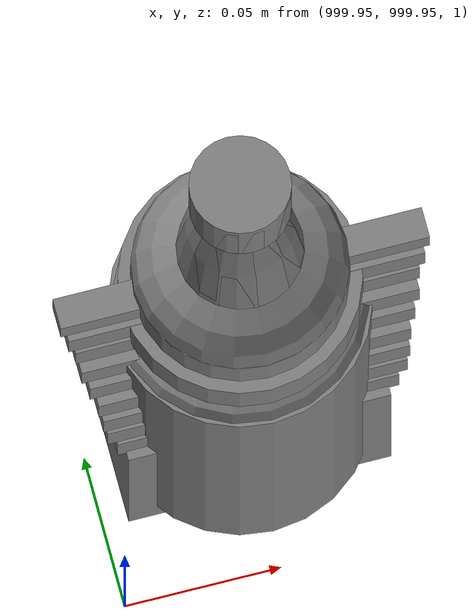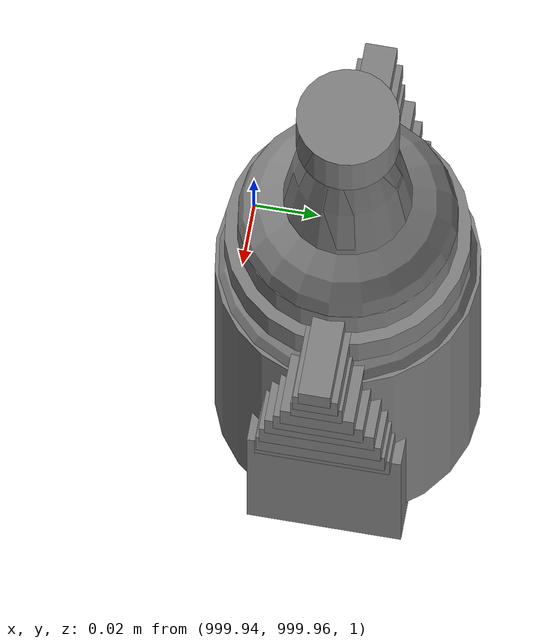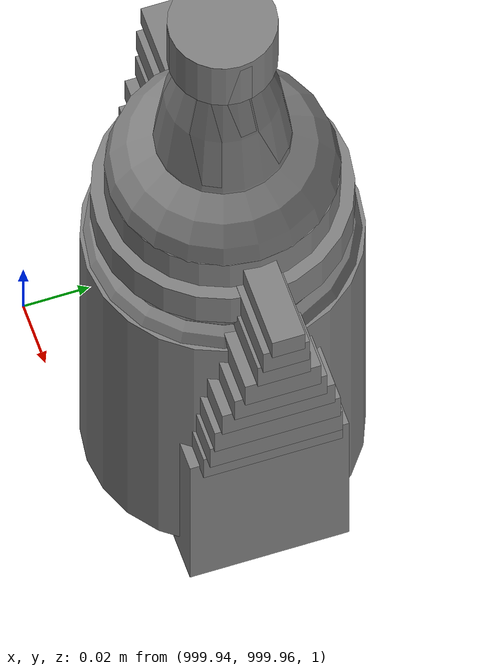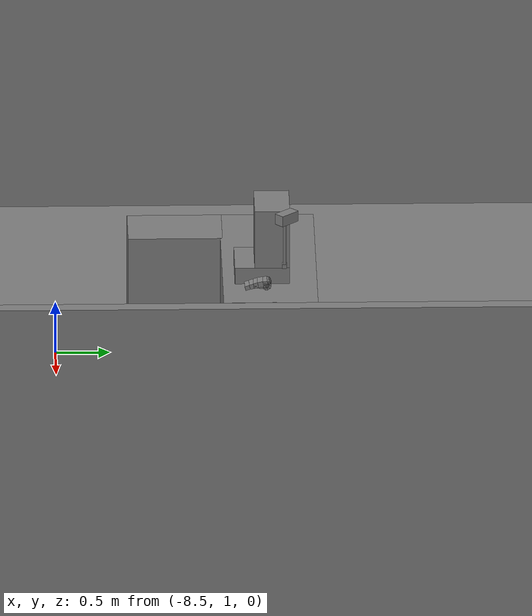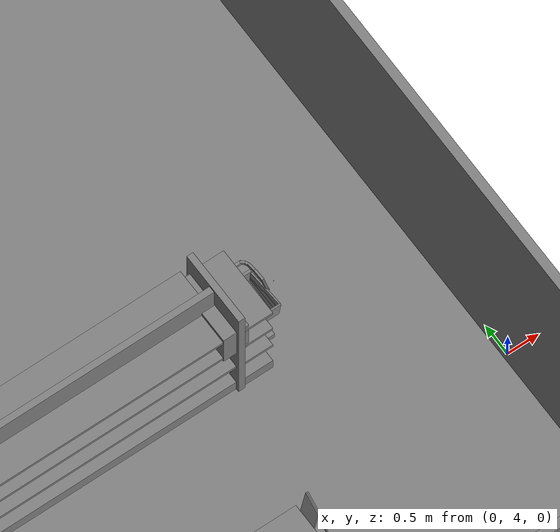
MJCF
<mujoco>
    <option gravity="0.000000000 0.000000000 -9.810000420" timestep="0.0166666" integrator="implicitfast" density="1.225" viscosity="1.8000001e-05" noslip_iterations="10" iterations="100" sdf_iterations="50">
        <flag multiccd="disable"/>
    </option>
    <size memory="1000M"/>
    <compiler coordinate="local"/>
    <worldbody>
        <light cutoff="30" pos="0 1 1" dir="0 -1 -2"/>
        <light cutoff="30" pos="0 -1 1" dir="0 1 -2"/>
        <body pos="0.000000000 0.000000000 0.000000000" euler="0.000000000 0.000000000 0.000000000" name="Interactive Objects_Interactive Objects"/>
        <body pos="-2.296927214 6.214255810 1.745231748" euler="-62.440608978 52.803112030 88.690406799" mocap="true" name="spotlight2_SpotLight"/>
        <body pos="1000.000000000 1000.000000000 1.000000000" euler="0.000000000 0.000000000 0.000000000" name="openloong_gripper_2f85_fix_base_usda_bottle_blue">
            <geom contype="1" conaffinity="1" density="1000" type="ellipsoid" material="" rgba="0.500000000 0.500000000 0.500000000 1.000000000" solimp="0.899999976 0.949999988 0.001000000" friction="1.000000000 0.005000000 0.000100000" solref="0.020000000 1.000000000" margin="0" condim="3" group="0" pos="0.000000000 0.000000000 0.118920922" quat="1.000000000 0.000000000 0.000000000 0.000000000" size="0.030999999 0.030999999 0.029999999" name="openloong_gripper_2f85_fix_base_usda_geom_1260DE0C_6F3D_4292_B368_6AEBAB1C92D2"/>
            <geom contype="1" conaffinity="1" density="1000" type="box" material="" rgba="0.500000000 0.500000000 0.500000000 1.000000000" solimp="0.899999976 0.949999988 0.001000000" friction="1.000000000 0.005000000 0.000100000" solref="0.020000000 1.000000000" margin="0" condim="3" group="0" pos="0.000000000 0.000000000 0.002164602" quat="1.000000000 0.000000000 0.000000000 0.000000000" size="0.020000000 0.020000000 0.003000000" name="openloong_gripper_2f85_fix_base_usda_geom_ABC5A0CF_4FE3_4D23_9E5E_2F3119142E13"/>
            <geom contype="1" conaffinity="1" density="1000" type="cylinder" material="" rgba="0.500000000 0.500000000 0.500000000 1.000000000" solimp="0.899999976 0.949999988 0.001000000" friction="1.000000000 0.005000000 0.000100000" solref="0.020000000 1.000000000" margin="0" condim="3" group="0" pos="0.000000000 -0.000366211 0.060859680" quat="1.000000000 0.000000000 0.000000000 0.000000000" size="0.030999999 0.057999998 1.000000000" name="openloong_gripper_2f85_fix_base_usda_geom_AC856C5F_1253_46E2_828C_A844113EE2D7"/>
            <geom contype="1" conaffinity="1" density="1000" type="cylinder" material="" rgba="0.500000000 0.500000000 0.500000000 1.000000000" solimp="0.899999976 0.949999988 0.001000000" friction="1.000000000 0.005000000 0.000100000" solref="0.020000000 1.000000000" margin="0" condim="3" group="0" pos="0.000000000 0.000000000 0.220594406" quat="1.000000000 0.000000000 0.000000000 0.000000000" size="0.016000001 0.010000000 1.000000000" name="openloong_gripper_2f85_fix_base_usda_geom_0034B20F_1AC0_4CE7_BAC0_D0C31CFEA0DA"/>
            <geom contype="1" conaffinity="1" density="1000" type="ellipsoid" material="" rgba="0.500000000 0.500000000 0.500000000 1.000000000" solimp="0.899999976 0.949999988 0.001000000" friction="1.000000000 0.005000000 0.000100000" solref="0.020000000 1.000000000" margin="0" condim="3" group="0" pos="0.000000000 0.000000000 0.144259930" quat="1.000000000 0.000000000 0.000000000 0.000000000" size="0.021000000 0.021000000 0.079999998" name="openloong_gripper_2f85_fix_base_usda_geom_2371C692_1082_4638_A88D_E1BE4A270D86"/>
            <freejoint name="openloong_gripper_2f85_fix_base_usda_bottle_blue_joint"/>
            <site size="0.005000000 0.005000000 0.005000000" rgba="0.500000000 0.500000000 0.500000000 1.000000000" pos="0.000000000 0.000000000 0.000000000" quat="0.999961913 0.008726535 0.000000000 0.000000000" group="0" type="sphere" name="openloong_gripper_2f85_fix_base_usda_bottle_bluesite"/>
        </body>
        <body pos="-2.080874681 6.337830067 1.699445128" euler="82.559967041 83.575370789 -145.655258179" mocap="true" name="spotlight1_SpotLight"/>
        <body pos="-2.145029306 6.231470108 1.674102306" euler="-157.285232544 66.702377319 -144.297927856" mocap="true" name="spotlight6_SpotLight"/>
        <body pos="1000.000000000 1000.000000000 1.000000000" euler="0.000000000 0.000000000 0.000000000" name="openloong_gripper_2f85_fix_base_usda_salt">
            <geom contype="1" conaffinity="1" density="1000" type="box" material="" rgba="0.500000000 0.500000000 0.500000000 1.000000000" solimp="0.899999976 0.949999988 0.001000000" friction="1.000000000 0.005000000 0.000100000" solref="0.020000000 1.000000000" margin="0" condim="3" group="0" pos="0.000305176 0.000000000 0.084862232" quat="1.000000000 0.000000000 0.000000000 0.000000000" size="0.048999999 0.018999999 0.005000000" name="openloong_gripper_2f85_fix_base_usda_geom_EAA2C72C_B63C_4265_A2EB_42A100F61E95"/>
            <geom contype="1" conaffinity="1" density="1000" type="box" material="" rgba="0.500000000 0.500000000 0.500000000 1.000000000" solimp="0.899999976 0.949999988 0.001000000" friction="1.000000000 0.005000000 0.000100000" solref="0.020000000 1.000000000" margin="0" condim="3" group="0" pos="0.000305176 0.000000000 0.104564309" quat="1.000000000 0.000000000 0.000000000 0.000000000" size="0.052000001 0.014000000 0.005000000" name="openloong_gripper_2f85_fix_base_usda_geom_7B905E93_E0CF_4505_AEAF_2B55FB43F8EF"/>
            <geom contype="1" conaffinity="1" density="1000" type="box" material="" rgba="0.500000000 0.500000000 0.500000000 1.000000000" solimp="0.899999976 0.949999988 0.001000000" friction="1.000000000 0.005000000 0.000100000" solref="0.020000000 1.000000000" margin="0" condim="3" group="0" pos="0.000305176 0.000000000 0.114487171" quat="1.000000000 0.000000000 0.000000000 0.000000000" size="0.054000001 0.011500000 0.005000000" name="openloong_gripper_2f85_fix_base_usda_geom_A28BA5A9_1655_4EBB_BC22_7DDF81C03F68"/>
            <geom contype="1" conaffinity="1" density="1000" type="box" material="" rgba="0.500000000 0.500000000 0.500000000 1.000000000" solimp="0.899999976 0.949999988 0.001000000" friction="1.000000000 0.005000000 0.000100000" solref="0.020000000 1.000000000" margin="0" condim="3" group="0" pos="0.000305176 0.000000000 0.075103164" quat="1.000000000 0.000000000 0.000000000 0.000000000" size="0.048000000 0.020000000 0.005000000" name="openloong_gripper_2f85_fix_base_usda_geom_6210920B_295B_4993_A9FB_6164FD2FFF45"/>
            <geom contype="1" conaffinity="1" density="1000" type="box" material="" rgba="0.500000000 0.500000000 0.500000000 1.000000000" solimp="0.899999976 0.949999988 0.001000000" friction="1.000000000 0.005000000 0.000100000" solref="0.020000000 1.000000000" margin="0" condim="3" group="0" pos="0.000305176 0.000000000 0.134892464" quat="1.000000000 0.000000000 0.000000000 0.000000000" size="0.057000000 0.007000000 0.005000000" name="openloong_gripper_2f85_fix_base_usda_geom_84E49646_2292_4406_A285_4F8EBF206CCC"/>
            <geom contype="1" conaffinity="1" density="1000" type="box" material="" rgba="0.500000000 0.500000000 0.500000000 1.000000000" solimp="0.899999976 0.949999988 0.001000000" friction="1.000000000 0.005000000 0.000100000" solref="0.020000000 1.000000000" margin="0" condim="3" group="0" pos="0.000305176 0.000000000 0.094920278" quat="1.000000000 0.000000000 0.000000000 0.000000000" size="0.050000001 0.017000001 0.005000000" name="openloong_gripper_2f85_fix_base_usda_geom_67A10B28_A7B6_40EF_94CE_4B47A1E6F1E9"/>
            <geom contype="1" conaffinity="1" density="1000" type="box" material="" rgba="0.500000000 0.500000000 0.500000000 1.000000000" solimp="0.899999976 0.949999988 0.001000000" friction="1.000000000 0.005000000 0.000100000" solref="0.020000000 1.000000000" margin="0" condim="3" group="0" pos="0.000305176 0.000000000 0.065204859" quat="1.000000000 0.000000000 0.000000000 0.000000000" size="0.045000002 0.021000000 0.005000000" name="openloong_gripper_2f85_fix_base_usda_geom_0F199501_FD39_4C15_A94C_74411294173A"/>
            <geom contype="1" conaffinity="1" density="1000" type="box" material="" rgba="0.500000000 0.500000000 0.500000000 1.000000000" solimp="0.899999976 0.949999988 0.001000000" friction="1.000000000 0.005000000 0.000100000" solref="0.020000000 1.000000000" margin="0" condim="3" group="0" pos="0.000305176 0.000000000 0.144135714" quat="1.000000000 0.000000000 0.000000000 0.000000000" size="0.059000000 0.005000000 0.004000000" name="openloong_gripper_2f85_fix_base_usda_geom_E65D0ACC_195D_4D7C_83F6_12FDC9C17251"/>
            <geom contype="1" conaffinity="1" density="1000" type="box" material="" rgba="0.500000000 0.500000000 0.500000000 1.000000000" solimp="0.899999976 0.949999988 0.001000000" friction="1.000000000 0.005000000 0.000100000" solref="0.020000000 1.000000000" margin="0" condim="3" group="0" pos="0.000000000 0.000000000 0.031593561" quat="1.000000000 0.000000000 0.000000000 0.000000000" size="0.041999999 0.024000000 0.029999999" name="openloong_gripper_2f85_fix_base_usda_geom_966DA27D_7215_42AA_80C2_0029D1156986"/>
            <geom contype="1" conaffinity="1" density="1000" type="box" material="" rgba="0.500000000 0.500000000 0.500000000 1.000000000" solimp="0.899999976 0.949999988 0.001000000" friction="1.000000000 0.005000000 0.000100000" solref="0.020000000 1.000000000" margin="0" condim="3" group="0" pos="0.000305176 0.000000000 0.124608755" quat="1.000000000 0.000000000 0.000000000 0.000000000" size="0.055000000 0.008000000 0.005000000" name="openloong_gripper_2f85_fix_base_usda_geom_A29D6537_8FA6_4E7C_95C9_F3BCD8F8242B"/>
            <freejoint name="openloong_gripper_2f85_fix_base_usda_salt_joint"/>
            <site size="0.005000000 0.005000000 0.005000000" rgba="0.500000000 0.500000000 0.500000000 1.000000000" pos="0.000000000 0.000000000 0.000000000" quat="1.000000000 0.000000000 0.000000000 0.000000000" group="0" type="sphere" name="openloong_gripper_2f85_fix_base_usda_saltsite"/>
        </body>
        <body pos="1000.000000000 1000.000000000 1.000000000" euler="0.000000000 0.000000000 0.000000000" name="openloong_gripper_2f85_fix_base_usda_bottle_red">
            <geom contype="1" conaffinity="1" density="1000" type="ellipsoid" material="" rgba="0.500000000 0.500000000 0.500000000 1.000000000" solimp="0.899999976 0.949999988 0.001000000" friction="1.000000000 0.005000000 0.000100000" solref="0.020000000 1.000000000" margin="0" condim="3" group="0" pos="0.000000000 0.000000000 0.144284487" quat="1.000000000 0.000000000 0.000000000 0.000000000" size="0.021000000 0.021000000 0.079999998" name="openloong_gripper_2f85_fix_base_usda_geom_37184C3F_3225_4D3C_9187_EF7260002317"/>
            <geom contype="1" conaffinity="1" density="1000" type="cylinder" material="" rgba="0.500000000 0.500000000 0.500000000 1.000000000" solimp="0.899999976 0.949999988 0.001000000" friction="1.000000000 0.005000000 0.000100000" solref="0.020000000 1.000000000" margin="0" condim="3" group="0" pos="0.000000000 0.000000000 0.220618963" quat="1.000000000 0.000000000 0.000000000 0.000000000" size="0.016000001 0.010000000 1.000000000" name="openloong_gripper_2f85_fix_base_usda_geom_2BB03C83_1DBA_4D88_8B25_FD9EB81081AC"/>
            <geom contype="1" conaffinity="1" density="1000" type="ellipsoid" material="" rgba="0.500000000 0.500000000 0.500000000 1.000000000" solimp="0.899999976 0.949999988 0.001000000" friction="1.000000000 0.005000000 0.000100000" solref="0.020000000 1.000000000" margin="0" condim="3" group="0" pos="0.000000000 0.000000000 0.118945479" quat="1.000000000 0.000000000 0.000000000 0.000000000" size="0.030999999 0.030999999 0.029999999" name="openloong_gripper_2f85_fix_base_usda_geom_8E6E0A25_87E8_47E9_84EC_BCFE37FCDD15"/>
            <geom contype="1" conaffinity="1" density="1000" type="box" material="" rgba="0.500000000 0.500000000 0.500000000 1.000000000" solimp="0.899999976 0.949999988 0.001000000" friction="1.000000000 0.005000000 0.000100000" solref="0.020000000 1.000000000" margin="0" condim="3" group="0" pos="0.000000000 0.000000000 0.002189159" quat="1.000000000 0.000000000 0.000000000 0.000000000" size="0.020000000 0.020000000 0.003000000" name="openloong_gripper_2f85_fix_base_usda_geom_05B5F07A_19EE_49D4_A0AC_67A97F968719"/>
            <geom contype="1" conaffinity="1" density="1000" type="cylinder" material="" rgba="0.500000000 0.500000000 0.500000000 1.000000000" solimp="0.899999976 0.949999988 0.001000000" friction="1.000000000 0.005000000 0.000100000" solref="0.020000000 1.000000000" margin="0" condim="3" group="0" pos="0.000000000 -0.000366211 0.060884237" quat="1.000000000 0.000000000 0.000000000 0.000000000" size="0.030999999 0.057999998 1.000000000" name="openloong_gripper_2f85_fix_base_usda_geom_1A5B3CD0_51DD_4632_9102_E9B02CF574B6"/>
            <freejoint name="openloong_gripper_2f85_fix_base_usda_bottle_red_joint"/>
            <site size="0.005000000 0.005000000 0.005000000" rgba="0.500000000 0.500000000 0.500000000 1.000000000" pos="0.000000000 0.000000000 0.000000000" quat="0.999961913 0.008726535 0.000000000 0.000000000" group="0" type="sphere" name="openloong_gripper_2f85_fix_base_usda_bottle_redsite"/>
        </body>
        <body pos="1000.000000000 1000.000000000 1.000000000" euler="0.000000000 0.000000000 0.000000000" name="openloong_gripper_2f85_fix_base_usda_jar_01">
            <geom contype="1" conaffinity="1" density="1000" type="box" material="" rgba="0.500000000 0.500000000 0.500000000 1.000000000" solimp="0.899999976 0.949999988 0.001000000" friction="1.000000000 0.005000000 0.000100000" solref="0.020000000 1.000000000" margin="0" condim="3" group="0" pos="0.000000000 0.000000000 0.006158113" quat="1.000000000 0.000000000 0.000000000 0.000000000" size="0.020000000 0.020000000 0.005000000" name="openloong_gripper_2f85_fix_base_usda_geom_948E3382_34F6_4E8E_AEE7_60A36588D581"/>
            <geom contype="1" conaffinity="1" density="1000" type="cylinder" material="" rgba="0.500000000 0.500000000 0.500000000 1.000000000" solimp="0.899999976 0.949999988 0.001000000" friction="1.000000000 0.005000000 0.000100000" solref="0.020000000 1.000000000" margin="0" condim="3" group="0" pos="0.000000000 0.000000000 0.062744498" quat="1.000000000 0.000000000 0.000000000 0.000000000" size="0.041000001 0.052999999 1.000000000" name="openloong_gripper_2f85_fix_base_usda_geom_0F15332F_B1FC_4C41_BDDF_FC5D415E6DC6"/>
            <geom contype="1" conaffinity="1" density="1000" type="ellipsoid" material="" rgba="0.500000000 0.500000000 0.500000000 1.000000000" solimp="0.899999976 0.949999988 0.001000000" friction="1.000000000 0.005000000 0.000100000" solref="0.020000000 1.000000000" margin="0" condim="3" group="0" pos="0.000000000 0.000000000 0.122252703" quat="1.000000000 0.000000000 0.000000000 0.000000000" size="0.035999998 0.035999998 0.010000000" name="openloong_gripper_2f85_fix_base_usda_geom_28F65EA7_8F79_4261_990C_60719DE3D747"/>
            <geom contype="1" conaffinity="1" density="1000" type="cylinder" material="" rgba="0.500000000 0.500000000 0.500000000 1.000000000" solimp="0.899999976 0.949999988 0.001000000" friction="1.000000000 0.005000000 0.000100000" solref="0.020000000 1.000000000" margin="0" condim="3" group="0" pos="0.000000000 0.000000000 0.015747190" quat="1.000000000 0.000000000 0.000000000 0.000000000" size="0.035000000 0.010000000 1.000000000" name="openloong_gripper_2f85_fix_base_usda_geom_ADA5ABED_1C69_460E_A27D_E93DE146A338"/>
            <geom contype="1" conaffinity="1" density="1000" type="ellipsoid" material="" rgba="0.500000000 0.500000000 0.500000000 1.000000000" solimp="0.899999976 0.949999988 0.001000000" friction="1.000000000 0.005000000 0.000100000" solref="0.020000000 1.000000000" margin="0" condim="3" group="0" pos="0.000000000 0.000000000 0.115815401" quat="1.000000000 0.000000000 0.000000000 0.000000000" size="0.039999999 0.039999999 0.010000000" name="openloong_gripper_2f85_fix_base_usda_geom_D262098E_8F11_485E_8F8F_904AAACDB504"/>
            <geom contype="1" conaffinity="1" density="1000" type="cylinder" material="" rgba="0.500000000 0.500000000 0.500000000 1.000000000" solimp="0.899999976 0.949999988 0.001000000" friction="1.000000000 0.005000000 0.000100000" solref="0.020000000 1.000000000" margin="0" condim="3" group="0" pos="0.000000000 0.000000000 0.133183479" quat="1.000000000 0.000000000 0.000000000 0.000000000" size="0.037999999 0.006500000 1.000000000" name="openloong_gripper_2f85_fix_base_usda_geom_D8962DD1_BD7D_4D79_AD9B_B3BF1FB402C2"/>
            <freejoint name="openloong_gripper_2f85_fix_base_usda_jar_01_joint"/>
            <site size="0.005000000 0.005000000 0.005000000" rgba="0.500000000 0.500000000 0.500000000 1.000000000" pos="0.000000000 0.000000000 0.000000000" quat="1.000000000 0.000000000 0.000000000 0.000000000" group="0" type="sphere" name="openloong_gripper_2f85_fix_base_usda_jar_01site"/>
        </body>
        <body pos="1000.000000000 1000.000000000 1.000000000" euler="0.000000000 0.000000000 0.000000000" name="openloong_gripper_2f85_fix_base_usda_can">
            <geom contype="1" conaffinity="1" density="1000" type="cylinder" material="" rgba="0.500000000 0.500000000 0.500000000 1.000000000" solimp="0.899999976 0.949999988 0.001000000" friction="1.000000000 0.005000000 0.000100000" solref="0.020000000 1.000000000" margin="0" condim="3" group="0" pos="0.000000000 0.000000000 0.079676986" quat="1.000000000 0.000000000 0.000000000 0.000000000" size="0.034000002 0.071999997 1.000000000" name="openloong_gripper_2f85_fix_base_usda_geom_E07F4F10_A1F4_4C1C_818E_B04F0C27FF8B"/>
            <geom contype="1" conaffinity="1" density="1000" type="ellipsoid" material="" rgba="0.500000000 0.500000000 0.500000000 1.000000000" solimp="0.899999976 0.949999988 0.001000000" friction="1.000000000 0.005000000 0.000100000" solref="0.020000000 1.000000000" margin="0" condim="3" group="0" pos="0.000000000 0.000000000 0.151854277" quat="1.000000000 0.000000000 0.000000000 0.000000000" size="0.034000002 0.034000002 0.020000000" name="openloong_gripper_2f85_fix_base_usda_geom_B6F3AF80_FE4B_471E_9029_8FA9E374F59E"/>
            <geom contype="1" conaffinity="1" density="1000" type="box" material="" rgba="0.500000000 0.500000000 0.500000000 1.000000000" solimp="0.899999976 0.949999988 0.001000000" friction="1.000000000 0.005000000 0.000100000" solref="0.020000000 1.000000000" margin="0" condim="3" group="0" pos="0.000000000 0.000000000 0.004777670" quat="1.000000000 0.000000000 0.000000000 0.000000000" size="0.020000000 0.020000000 0.005000000" name="openloong_gripper_2f85_fix_base_usda_geom_DB9E37C2_3A4B_4B0B_808A_63069CCC2C07"/>
            <freejoint name="openloong_gripper_2f85_fix_base_usda_can_joint"/>
            <site size="0.005000000 0.005000000 0.005000000" rgba="0.500000000 0.500000000 0.500000000 1.000000000" pos="0.000000000 0.000000000 0.000000000" quat="1.000000000 0.000000000 0.000000000 0.000000000" group="0" type="sphere" name="openloong_gripper_2f85_fix_base_usda_cansite"/>
        </body>
        <body pos="0.000000000 0.000000000 0.000000000" euler="0.000000000 0.000000000 0.000000000" name=" Static Objects_ Static Objects">
            <geom contype="1" conaffinity="1" density="1000" type="box" material="" rgba="0.500000000 0.500000000 0.500000000 1.000000000" solimp="0.899999976 0.949999988 0.001000000" friction="1.000000000 0.005000000 0.000100000" solref="0.020000000 1.000000000" margin="0" condim="3" group="0" pos="-6.286010742 6.153595448 1.563861728" quat="0.707107067 0.000000000 0.000000000 0.707106471" size="0.529999971 3.134999990 0.025000000" name=" Static Objects_geom_459BDEFF_C2F4_42BC_AC04_5D3FA4A671F5"/>
            <geom contype="1" conaffinity="1" density="1000" type="box" material="" rgba="0.500000000 0.500000000 0.500000000 1.000000000" solimp="0.899999976 0.949999988 0.001000000" friction="1.000000000 0.005000000 0.000100000" solref="0.020000000 1.000000000" margin="0" condim="3" group="0" pos="-3.101639986 6.150595188 1.018643856" quat="1.000000000 0.000000000 0.000000000 0.000000000" size="0.050000001 0.579999983 1.019999981" name=" Static Objects_geom_AB6392E8_1211_41AA_93B3_E98BE69FC799"/>
            <geom contype="1" conaffinity="1" density="1000" type="box" material="" rgba="0.500000000 0.500000000 0.500000000 1.000000000" solimp="0.899999976 0.949999988 0.001000000" friction="1.000000000 0.005000000 0.000100000" solref="0.020000000 1.000000000" margin="0" condim="3" group="0" pos="-2.825197220 6.153595448 1.563861728" quat="0.707107067 0.000000000 0.000000000 0.707106471" size="0.550000012 0.239999995 0.025000000" name=" Static Objects_geom_2BC84F8B_AC27_4AB3_BFFD_640EC3447AD6"/>
            <geom contype="1" conaffinity="1" density="1000" type="box" material="" rgba="0.500000000 0.500000000 0.500000000 1.000000000" solimp="0.899999976 0.949999988 0.001000000" friction="1.000000000 0.005000000 0.000100000" solref="0.020000000 1.000000000" margin="0" condim="3" group="0" pos="-6.311686516 6.153595448 1.018643856" quat="0.707107067 0.000000000 0.000000000 0.707106471" size="0.050000001 3.150000095 1.019999981" name=" Static Objects_geom_71C384AD_885A_4998_A757_ACA776D70620"/>
            <geom contype="1" conaffinity="1" density="1000" type="box" material="" rgba="0.500000000 0.500000000 0.500000000 1.000000000" solimp="0.899999976 0.949999988 0.001000000" friction="1.000000000 0.005000000 0.000100000" solref="0.020000000 1.000000000" margin="0" condim="3" group="0" pos="-2.825197220 6.153595448 1.115278244" quat="0.707107067 0.000000000 0.000000000 0.707106471" size="0.550000012 0.239999995 0.025000000" name=" Static Objects_geom_F4A3C101_EE0C_4366_BB2E_CF73585D7081"/>
            <geom contype="1" conaffinity="1" density="1000" type="box" material="" rgba="0.500000000 0.500000000 0.500000000 1.000000000" solimp="0.899999976 0.949999988 0.001000000" friction="1.000000000 0.005000000 0.000100000" solref="0.020000000 1.000000000" margin="0" condim="3" group="0" pos="-6.293097973 6.153595448 1.114443064" quat="0.707107067 0.000000000 0.000000000 0.707106471" size="0.529999971 3.134999990 0.025000000" name=" Static Objects_geom_7F49B9CB_1860_46D8_9954_0638150E9C28"/>
            <geom contype="1" conaffinity="1" density="1000" type="box" material="" rgba="0.500000000 0.500000000 0.500000000 1.000000000" solimp="0.899999976 0.949999988 0.001000000" friction="1.000000000 0.005000000 0.000100000" solref="0.020000000 1.000000000" margin="0" condim="3" group="0" pos="-2.825197220 6.153595448 0.629031777" quat="0.707107067 0.000000000 0.000000000 0.707106471" size="0.550000012 0.239999995 0.025000000" name=" Static Objects_geom_EBD4F840_55D5_4B58_9005_3E728D7FD3A4"/>
            <geom contype="1" conaffinity="1" density="1000" type="box" material="" rgba="0.500000000 0.500000000 0.500000000 1.000000000" solimp="0.899999976 0.949999988 0.001000000" friction="1.000000000 0.005000000 0.000100000" solref="0.020000000 1.000000000" margin="0" condim="3" group="0" pos="-6.286010742 6.153595448 0.096129179" quat="0.707107067 0.000000000 0.000000000 0.707106471" size="0.529999971 3.134999990 0.098999999" name=" Static Objects_geom_4047C9CA_6C6E_4293_A594_95971638B09F"/>
            <geom contype="1" conaffinity="1" density="1000" type="box" material="" rgba="0.500000000 0.500000000 0.500000000 1.000000000" solimp="0.899999976 0.949999988 0.001000000" friction="1.000000000 0.005000000 0.000100000" solref="0.020000000 1.000000000" margin="0" condim="3" group="0" pos="-2.825197220 6.153595448 0.097434282" quat="0.707107067 0.000000000 0.000000000 0.707106471" size="0.550000012 0.239999995 0.098999999" name=" Static Objects_geom_BD764944_FC5F_4353_BE63_837D4CD949AD"/>
            <geom contype="1" conaffinity="1" density="1000" type="box" material="" rgba="0.500000000 0.500000000 0.500000000 1.000000000" solimp="0.899999976 0.949999988 0.001000000" friction="1.000000000 0.005000000 0.000100000" solref="0.020000000 1.000000000" margin="0" condim="3" group="0" pos="-6.286010742 6.153595448 0.629031777" quat="0.707107067 0.000000000 0.000000000 0.707106471" size="0.529999971 3.134999990 0.025000000" name=" Static Objects_geom_58AD867A_6B8A_41AE_A273_3DF6F3B41096"/>
            <geom contype="1" conaffinity="1" density="1000" type="box" material="" rgba="0.500000000 0.500000000 0.500000000 1.000000000" solimp="0.899999976 0.949999988 0.001000000" friction="1.000000000 0.005000000 0.000100000" solref="0.020000000 1.000000000" margin="0" condim="3" group="0" pos="-6.000000000 20.159999847 2.000000000" quat="1.000000000 0.000000000 0.000000000 0.000000000" size="6.079999924 0.070000000 2.000000000" name=" Static Objects_geom_4E35E90B_131B_4C22_BB1E_A441FE019D71"/>
            <geom contype="1" conaffinity="1" density="1000" type="box" material="" rgba="0.500000000 0.500000000 0.500000000 1.000000000" solimp="0.899999976 0.949999988 0.001000000" friction="1.000000000 0.005000000 0.000100000" solref="0.020000000 1.000000000" margin="0" condim="3" group="0" pos="-6.000000000 0.035000000 2.000000000" quat="1.000000000 0.000000000 0.000000000 0.000000000" size="6.079999924 0.070000000 2.000000000" name=" Static Objects_geom_DFDCF5F1_D915_4994_897F_42F3435BFDA6"/>
            <geom contype="1" conaffinity="1" density="1000" type="box" material="" rgba="0.500000000 0.500000000 0.500000000 1.000000000" solimp="0.899999976 0.949999988 0.001000000" friction="1.000000000 0.005000000 0.000100000" solref="0.020000000 1.000000000" margin="0" condim="3" group="0" pos="0.000000000 10.000000000 2.000000000" quat="1.000000000 0.000000000 0.000000000 0.000000000" size="0.070000000 10.500000000 2.000000000" name=" Static Objects_geom_E736F606_E76B_4034_BC77_56F87D6E8247"/>
            <geom contype="1" conaffinity="1" density="1000" type="box" material="" rgba="0.500000000 0.500000000 0.500000000 1.000000000" solimp="0.899999976 0.949999988 0.001000000" friction="1.000000000 0.005000000 0.000100000" solref="0.020000000 1.000000000" margin="0" condim="3" group="0" pos="-12.050000191 10.000000000 2.000000000" quat="1.000000000 0.000000000 0.000000000 0.000000000" size="0.070000000 10.500000000 2.000000000" name=" Static Objects_geom_9481AC9D_9BD1_4813_8C53_0807AB482A10"/>
            <geom contype="1" conaffinity="1" density="1000" type="plane" material="" rgba="0.500000000 0.500000000 0.500000000 1.000000000" solimp="0.899999976 0.949999988 0.001000000" friction="1.000000000 0.005000000 0.000100000" solref="0.020000000 1.000000000" margin="0" condim="3" group="0" pos="-6.000000000 10.399999619 0.000000000" quat="1.000000000 0.000000000 0.000000000 0.000000000" size="6.050000191 10.800000191 0.010000000" name=" Static Objects_geom_3B829DFC_9F89_44E1_B1C0_0E6A267047CE"/>
            <geom contype="1" conaffinity="1" density="1000" type="box" material="" rgba="0.500000000 0.500000000 0.500000000 1.000000000" solimp="0.899999976 0.949999988 0.001000000" friction="1.000000000 0.005000000 0.000100000" solref="0.020000000 1.000000000" margin="0" condim="3" group="0" pos="-8.830721855 2.096410990 0.549305558" quat="1.000000000 0.000000000 0.000000000 0.000000000" size="0.280000001 0.430000007 0.550000012" name=" Static Objects_geom_21F86C60_A535_4772_B501_78E75C8B647A"/>
            <geom contype="1" conaffinity="1" density="1000" type="box" material="" rgba="0.500000000 0.500000000 0.500000000 1.000000000" solimp="0.899999976 0.949999988 0.001000000" friction="1.000000000 0.005000000 0.000100000" solref="0.020000000 1.000000000" margin="0" condim="3" group="0" pos="-6.460197449 2.937205315 0.548931718" quat="1.000000000 0.000000000 0.000000000 0.000000000" size="2.650000095 0.430000007 0.550000012" name=" Static Objects_geom_4CCFAF2B_F1A7_4676_9966_7C58B0BE9E3C"/>
            <geom contype="1" conaffinity="1" density="1000" type="box" material="" rgba="0.500000000 0.500000000 0.500000000 1.000000000" solimp="0.899999976 0.949999988 0.001000000" friction="1.000000000 0.005000000 0.000100000" solref="0.020000000 1.000000000" margin="0" condim="3" group="0" pos="-4.240264893 1.327049494 0.549888909" quat="1.000000000 0.000000000 0.000000000 0.000000000" size="0.430000007 1.200000048 0.550000012" name=" Static Objects_geom_F57C3785_A551_41D9_A87C_A6CDED9CF180"/>
            <geom contype="1" conaffinity="1" density="1000" type="box" material="" rgba="0.500000000 0.500000000 0.500000000 1.000000000" solimp="0.899999976 0.949999988 0.001000000" friction="1.000000000 0.005000000 0.000100000" solref="0.020000000 1.000000000" margin="0" condim="3" group="0" pos="-7.408766270 3.088089943 1.776644945" quat="0.928051054 0.000000000 0.000000000 0.372453064" size="0.050000001 0.100000001 0.050000001" name=" Static Objects_geom_0E299B1D_B02B_4793_A084_B69DAC795895"/>
            <geom contype="1" conaffinity="1" density="1000" type="box" material="" rgba="0.500000000 0.500000000 0.500000000 1.000000000" solimp="0.899999976 0.949999988 0.001000000" friction="1.000000000 0.005000000 0.000100000" solref="0.020000000 1.000000000" margin="0" condim="3" group="0" pos="-7.437745571 3.067511320 1.289965630" quat="1.000000000 0.000000000 0.000000000 0.000000000" size="0.029999999 0.020000000 0.020000000" name=" Static Objects_geom_9DE9FC98_A703_4003_A8C5_800F867DEB46"/>
            <geom contype="1" conaffinity="1" density="1000" type="box" material="" rgba="0.500000000 0.500000000 0.500000000 1.000000000" solimp="0.899999976 0.949999988 0.001000000" friction="1.000000000 0.005000000 0.000100000" solref="0.020000000 1.000000000" margin="0" condim="3" group="0" pos="-7.719123363 2.867671013 1.173410416" quat="1.000000000 0.000000000 0.000000000 0.000000000" size="0.250000000 0.250000000 0.079999998" name=" Static Objects_geom_BB064C5A_160E_499A_AA12_87388065DCA7"/>
            <geom contype="1" conaffinity="1" density="1000" type="box" material="" rgba="0.500000000 0.500000000 0.500000000 1.000000000" solimp="0.899999976 0.949999988 0.001000000" friction="1.000000000 0.005000000 0.000100000" solref="0.020000000 1.000000000" margin="0" condim="3" group="0" pos="-7.719123363 2.958004713 1.530241251" quat="1.000000000 0.000000000 0.000000000 0.000000000" size="0.250000000 0.159999996 0.280000001" name=" Static Objects_geom_CF3712DA_00A3_4C4A_8D63_3AE04B119214"/>
            <geom contype="1" conaffinity="1" density="1000" type="cylinder" material="" rgba="0.500000000 0.500000000 0.500000000 1.000000000" solimp="0.899999976 0.949999988 0.001000000" friction="1.000000000 0.005000000 0.000100000" solref="0.020000000 1.000000000" margin="0" condim="3" group="0" pos="-7.427312374 3.069516420 1.502544641" quat="0.928051054 0.000000000 0.000000000 0.372453064" size="0.015000000 0.230000004 0.100000001" name=" Static Objects_geom_E72713AA_AA09_46C3_A2EB_0F7BE5AA58C6"/>
            <geom contype="1" conaffinity="1" density="1000" type="box" material="" rgba="0.500000000 0.500000000 0.500000000 1.000000000" solimp="0.899999976 0.949999988 0.001000000" friction="1.000000000 0.005000000 0.000100000" solref="0.020000000 1.000000000" margin="0" condim="3" group="0" pos="-9.058088303 6.434794426 1.209077358" quat="1.000000000 0.000000000 0.000000000 0.000000000" size="0.250000000 0.100000001 0.070000000" name=" Static Objects_geom_8B460B14_F0FE_48BB_93C6_601B89B0CFA7"/>
            <geom contype="1" conaffinity="1" density="1000" type="box" material="" rgba="0.500000000 0.500000000 0.500000000 1.000000000" solimp="0.899999976 0.949999988 0.001000000" friction="1.000000000 0.005000000 0.000100000" solref="0.020000000 1.000000000" margin="0" condim="3" group="0" pos="-5.611940861 6.318420410 0.350975692" quat="1.000000000 0.000000000 0.000000000 0.000000000" size="0.699999988 0.100000001 0.150000006" name=" Static Objects_geom_46FEC219_D149_4436_BF46_86298323CC39"/>
            <geom contype="1" conaffinity="1" density="1000" type="box" material="" rgba="0.500000000 0.500000000 0.500000000 1.000000000" solimp="0.899999976 0.949999988 0.001000000" friction="1.000000000 0.005000000 0.000100000" solref="0.020000000 1.000000000" margin="0" condim="3" group="0" pos="-9.237723351 6.464855671 1.209077358" quat="1.000000000 0.000000000 0.000000000 0.000000000" size="0.100000001 0.100000001 0.070000000" name=" Static Objects_geom_A3D21156_0070_49CC_8472_AD8F44659DA1"/>
            <geom contype="1" conaffinity="1" density="1000" type="box" material="" rgba="0.500000000 0.500000000 0.500000000 1.000000000" solimp="0.899999976 0.949999988 0.001000000" friction="1.000000000 0.005000000 0.000100000" solref="0.020000000 1.000000000" margin="0" condim="3" group="0" pos="-6.300771236 6.459744930 1.744376063" quat="1.000000000 0.000000000 0.000000000 0.000000000" size="3.000000000 0.200000003 0.150000006" name=" Static Objects_geom_77DC9E8B_7751_44F7_91D6_F7CB5E6B38D1"/>
            <geom contype="1" conaffinity="1" density="1000" type="box" material="" rgba="0.500000000 0.500000000 0.500000000 1.000000000" solimp="0.899999976 0.949999988 0.001000000" friction="1.000000000 0.005000000 0.000100000" solref="0.020000000 1.000000000" margin="0" condim="3" group="0" pos="-7.373087406 6.458900928 1.214329123" quat="1.000000000 0.000000000 0.000000000 0.000000000" size="0.250000000 0.200000003 0.075000003" name=" Static Objects_geom_B3496807_7BF8_4A4C_88D2_5297E6E812FE"/>
            <geom contype="1" conaffinity="1" density="1000" type="box" material="" rgba="0.500000000 0.500000000 0.500000000 1.000000000" solimp="0.899999976 0.949999988 0.001000000" friction="1.000000000 0.005000000 0.000100000" solref="0.020000000 1.000000000" margin="0" condim="3" group="0" pos="-4.035642624 6.459744930 0.352518857" quat="1.000000000 0.000000000 0.000000000 0.000000000" size="0.800000012 0.200000003 0.150000006" name=" Static Objects_geom_7CF2C2FE_747C_4403_8182_1D170D6ACD3D"/>
            <geom contype="1" conaffinity="1" density="1000" type="box" material="" rgba="0.500000000 0.500000000 0.500000000 1.000000000" solimp="0.899999976 0.949999988 0.001000000" friction="1.000000000 0.005000000 0.000100000" solref="0.020000000 1.000000000" margin="0" condim="3" group="0" pos="-3.907610416 6.318625927 0.800981164" quat="1.000000000 0.000000000 0.000000000 0.000000000" size="0.500000000 0.100000001 0.150000006" name=" Static Objects_geom_0E1F99BF_8357_4E12_9B29_989352CB0FBC"/>
            <geom contype="1" conaffinity="1" density="1000" type="box" material="" rgba="0.500000000 0.500000000 0.500000000 1.000000000" solimp="0.899999976 0.949999988 0.001000000" friction="1.000000000 0.005000000 0.000100000" solref="0.020000000 1.000000000" margin="0" condim="3" group="0" pos="-6.098561764 6.327973843 1.292199373" quat="1.000000000 0.000000000 0.000000000 0.000000000" size="0.500000000 0.100000001 0.150000006" name=" Static Objects_geom_0581FC7C_B983_4F7F_9411_23EE6E1176A4"/>
            <geom contype="1" conaffinity="1" density="1000" type="box" material="" rgba="0.500000000 0.500000000 0.500000000 1.000000000" solimp="0.899999976 0.949999988 0.001000000" friction="1.000000000 0.005000000 0.000100000" solref="0.020000000 1.000000000" margin="0" condim="3" group="0" pos="-7.886891365 6.459744930 0.352518857" quat="1.000000000 0.000000000 0.000000000 0.000000000" size="1.500000000 0.200000003 0.150000006" name=" Static Objects_geom_42179EFC_172A_4011_AF8C_B10974E8B402"/>
            <geom contype="1" conaffinity="1" density="1000" type="box" material="" rgba="0.500000000 0.500000000 0.500000000 1.000000000" solimp="0.899999976 0.949999988 0.001000000" friction="1.000000000 0.005000000 0.000100000" solref="0.020000000 1.000000000" margin="0" condim="3" group="0" pos="-6.824534416 6.447464466 1.212718010" quat="1.000000000 0.000000000 0.000000000 0.000000000" size="0.100000001 0.100000001 0.075000003" name=" Static Objects_geom_84B993EF_397B_48BE_BDFA_662F49E68F88"/>
            <geom contype="1" conaffinity="1" density="1000" type="box" material="" rgba="0.500000000 0.500000000 0.500000000 1.000000000" solimp="0.899999976 0.949999988 0.001000000" friction="1.000000000 0.005000000 0.000100000" solref="0.020000000 1.000000000" margin="0" condim="3" group="0" pos="-4.407354832 6.459744930 1.292199373" quat="1.000000000 0.000000000 0.000000000 0.000000000" size="1.240000010 0.200000003 0.150000006" name=" Static Objects_geom_9751A84E_F82C_49D7_B456_18DCD9213AD5"/>
            <geom contype="1" conaffinity="1" density="1000" type="box" material="" rgba="0.500000000 0.500000000 0.500000000 1.000000000" solimp="0.899999976 0.949999988 0.001000000" friction="1.000000000 0.005000000 0.000100000" solref="0.020000000 1.000000000" margin="0" condim="3" group="0" pos="-6.751636982 6.459744930 0.800981164" quat="1.000000000 0.000000000 0.000000000 0.000000000" size="2.200000048 0.200000003 0.150000006" name=" Static Objects_geom_386AA16A_6E8D_447C_AA0B_B84EAF6279B2"/>
            <geom contype="1" conaffinity="1" density="1000" type="box" material="" rgba="0.500000000 0.500000000 0.500000000 1.000000000" solimp="0.899999976 0.949999988 0.001000000" friction="1.000000000 0.005000000 0.000100000" solref="0.020000000 1.000000000" margin="0" condim="3" group="0" pos="-6.924745083 6.362090111 1.214329123" quat="1.000000000 0.000000000 0.000000000 0.000000000" size="0.200000003 0.100000001 0.075000003" name=" Static Objects_geom_7ECFFFAF_6243_4403_905B_216BF915EA7D"/>
            <geom contype="1" conaffinity="1" density="1000" type="box" material="" rgba="0.500000000 0.500000000 0.500000000 1.000000000" solimp="0.899999976 0.949999988 0.001000000" friction="1.000000000 0.005000000 0.000100000" solref="0.020000000 1.000000000" margin="0" condim="3" group="0" pos="-8.844120979 6.464855671 1.209077358" quat="1.000000000 0.000000000 0.000000000 0.000000000" size="0.100000001 0.100000001 0.070000000" name=" Static Objects_geom_6AB5EB14_8C44_4B6E_BE65_F237029E0341"/>
            <geom contype="1" conaffinity="1" density="1000" type="box" material="" rgba="0.500000000 0.500000000 0.500000000 1.000000000" solimp="0.899999976 0.949999988 0.001000000" friction="1.000000000 0.005000000 0.000100000" solref="0.020000000 1.000000000" margin="0" condim="3" group="0" pos="-3.157672644 6.136868477 1.348373055" quat="1.000000000 0.000000000 0.000000000 0.000000000" size="0.200000003 0.519999981 0.300000012" name=" Static Objects_geom_39BA68A3_450E_4CBD_B114_DCB596FDB1DB"/>
        </body>
        <body pos="-6.332345009 2.779978037 1.034067392" euler="0.000000000 0.000000000 0.000000000" name="openloong_gripper_2f85_fix_base_usda_basket">
            <geom contype="1" conaffinity="1" density="100000" type="box" material="" rgba="0.500000000 0.500000000 0.500000000 1.000000000" solimp="0.899999976 0.949999988 0.001000000" friction="1.000000000 0.899999976 0.000100000" solref="0.020000000 1.000000000" margin="0" condim="3" group="0" pos="-0.039724827 -0.188568115 0.167089701" quat="0.997537494 0.070135131 0.000000000 0.000000000" size="0.150000006 0.006000000 0.108000003" name="openloong_gripper_2f85_fix_base_usda_geom_59887FEE_737B_4362_9DA7_AC706A90CBFB"/>
            <geom contype="1" conaffinity="1" density="100000" type="box" material="" rgba="0.500000000 0.500000000 0.500000000 1.000000000" solimp="0.899999976 0.949999988 0.001000000" friction="1.000000000 0.899999976 0.000100000" solref="0.020000000 1.000000000" margin="0" condim="3" group="0" pos="0.094372749 0.000000000 0.168361664" quat="0.706172049 0.036353335 0.036353379 0.706171215" size="0.200000003 0.006000000 0.108000003" name="openloong_gripper_2f85_fix_base_usda_geom_875927DB_5405_4332_B7C5_2CC043C892D0"/>
            <geom contype="1" conaffinity="1" density="100000" type="box" material="" rgba="0.500000000 0.500000000 0.500000000 1.000000000" solimp="0.899999976 0.949999988 0.001000000" friction="1.000000000 0.899999976 0.000100000" solref="0.020000000 1.000000000" margin="0" condim="3" group="0" pos="-0.039724827 0.000000000 0.068126202" quat="1.000000000 0.000000000 0.000000000 0.000000000" size="0.129999995 0.174999997 0.006000000" name="openloong_gripper_2f85_fix_base_usda_geom_7A479170_EA84_40B8_880C_8C731483A1F4"/>
            <geom contype="1" conaffinity="1" density="100000" type="box" material="" rgba="0.500000000 0.500000000 0.500000000 1.000000000" solimp="0.899999976 0.949999988 0.001000000" friction="1.000000000 0.899999976 0.000100000" solref="0.020000000 1.000000000" margin="0" condim="3" group="0" pos="-0.039724827 0.188377380 0.167089701" quat="0.997489929 -0.070808925 0.000000000 0.000000000" size="0.150000006 0.006000000 0.108000003" name="openloong_gripper_2f85_fix_base_usda_geom_83671E3D_797B_444E_BF1F_2819921DE6BF"/>
            <geom contype="1" conaffinity="1" density="100000" type="box" material="" rgba="0.500000000 0.500000000 0.500000000 1.000000000" solimp="0.899999976 0.949999988 0.001000000" friction="1.000000000 0.899999976 0.000100000" solref="0.020000000 1.000000000" margin="0" condim="3" group="0" pos="-0.172339439 0.000000000 0.168361664" quat="0.706172407 -0.036353018 -0.036353093 0.706170976" size="0.200000003 0.006000000 0.108000003" name="openloong_gripper_2f85_fix_base_usda_geom_8DF3B9BC_7A28_4C3E_913F_3955A156B116"/>
            <freejoint name="openloong_gripper_2f85_fix_base_usda_basket_joint"/>
            <site size="0.005000000 0.005000000 0.005000000" rgba="0.500000000 0.500000000 0.500000000 1.000000000" pos="0.000000000 0.000000000 0.000000000" quat="1.000000000 0.000000000 0.000000000 0.000000000" group="0" type="sphere" name="openloong_gripper_2f85_fix_base_usda_basketsite"/>
        </body>
        <body pos="-3.510578632 3.403555870 -0.000000100" euler="0.000000000 0.000000000 40.200675964" name="openloong_gripper_2f85_fix_base_usda_PZ">
            <geom contype="1" conaffinity="1" density="1000" type="box" material="" rgba="0.500000000 0.500000000 0.500000000 1.000000000" solimp="0.899999976 0.949999988 0.001000000" friction="1.000000000 0.005000000 0.000100000" solref="0.020000000 1.000000000" margin="0" condim="3" group="0" pos="-0.047453165 0.056484699 0.373715430" quat="0.934750080 0.077914521 0.028795123 0.345459938" size="0.180000007 0.010000000 0.379999995" name="openloong_gripper_2f85_fix_base_usda_geom_46E2952E_B248_44BA_8E1F_5DA223811072"/>
            <geom contype="1" conaffinity="1" density="1000" type="box" material="" rgba="0.500000000 0.500000000 0.500000000 1.000000000" solimp="0.899999976 0.949999988 0.001000000" friction="1.000000000 0.005000000 0.000100000" solref="0.020000000 1.000000000" margin="0" condim="3" group="0" pos="0.047452450 -0.054376602 0.374072611" quat="0.934387863 -0.082143910 -0.030358355 0.345326364" size="0.180000007 0.010000000 0.379999995" name="openloong_gripper_2f85_fix_base_usda_geom_9208B9DE_3D06_4B78_9F00_E779C1E9C1B1"/>
            <freejoint name="openloong_gripper_2f85_fix_base_usda_PZ"/>
        </body>
        <body pos="-7.168000221 2.823999882 1.227496982" euler="-0.283413976 0.056829724 -0.133293271" name="openloong_gripper_2f85_fix_base_usda_Pos">
            <geom contype="1" conaffinity="1" density="1000" type="box" material="" rgba="0.500000000 0.500000000 0.500000000 1.000000000" solimp="0.899999976 0.949999988 0.001000000" friction="1.000000000 0.005000000 0.000100000" solref="0.020000000 1.000000000" margin="0" condim="3" group="0" pos="-0.002278805 0.074524641 -0.004134059" quat="0.315989345 0.948763072 -0.000000000 0.000000000" size="0.059999999 0.013000000 0.035000000" name="openloong_gripper_2f85_fix_base_usda_geom_8D3BB951_445C_4E0D_B919_82CB1BF14B97"/>
            <geom contype="1" conaffinity="1" density="1000" type="box" material="" rgba="0.500000000 0.500000000 0.500000000 1.000000000" solimp="0.899999976 0.949999988 0.001000000" friction="1.000000000 0.005000000 0.000100000" solref="0.020000000 1.000000000" margin="0" condim="3" group="0" pos="-0.002278805 0.078031301 0.008128285" quat="0.990447521 -0.137893379 -0.000000000 -0.000000000" size="0.059999999 0.010000000 0.035000000" name="openloong_gripper_2f85_fix_base_usda_geom_9E389704_7971_46C1_A217_2A573EB63B44"/>
            <geom contype="1" conaffinity="1" density="1000" type="box" material="" rgba="0.500000000 0.500000000 0.500000000 1.000000000" solimp="0.899999976 0.949999988 0.001000000" friction="1.000000000 0.005000000 0.000100000" solref="0.020000000 1.000000000" margin="0" condim="3" group="0" pos="-0.002278805 0.080785275 -0.002596974" quat="0.287325472 -0.957833409 0.000000000 -0.000000000" size="0.059999999 0.013000000 0.035000000" name="openloong_gripper_2f85_fix_base_usda_geom_62AF6648_C91E_41A8_B946_A789F9564B72"/>
            <geom contype="1" conaffinity="1" density="1000" type="box" material="" rgba="0.500000000 0.500000000 0.500000000 1.000000000" solimp="0.899999976 0.949999988 0.001000000" friction="1.000000000 0.005000000 0.000100000" solref="0.020000000 1.000000000" margin="0" condim="3" group="0" pos="-0.002278805 -0.098804474 -0.020146966" quat="0.988851666 0.148906454 0.000000000 -0.000000000" size="0.059999999 0.022000000 0.020000000" name="openloong_gripper_2f85_fix_base_usda_geom_D70D3879_D90E_4E88_962F_CC3E50BACC99"/>
            <geom contype="1" conaffinity="1" density="1000" type="box" material="" rgba="0.500000000 0.500000000 0.500000000 1.000000000" solimp="0.899999976 0.949999988 0.001000000" friction="1.000000000 0.005000000 0.000100000" solref="0.020000000 1.000000000" margin="0" condim="3" group="0" pos="-0.002279282 0.019920111 0.012102962" quat="0.995421767 0.095583342 -0.000000000 -0.000000000" size="0.059999999 0.025000000 0.026000001" name="openloong_gripper_2f85_fix_base_usda_geom_DD9DD619_5BA0_42E5_BF14_75CF4DA52901"/>
            <geom contype="1" conaffinity="1" density="1000" type="box" material="" rgba="0.500000000 0.500000000 0.500000000 1.000000000" solimp="0.899999976 0.949999988 0.001000000" friction="1.000000000 0.005000000 0.000100000" solref="0.020000000 1.000000000" margin="0" condim="3" group="0" pos="-0.002279282 0.005734444 -0.014276862" quat="0.999571741 -0.029275302 -0.000000000 -0.000000000" size="0.059999999 0.050000001 0.010000000" name="openloong_gripper_2f85_fix_base_usda_geom_149187C2_3EBF_4D1B_A523_D639A7F14CA8"/>
            <geom contype="1" conaffinity="1" density="1000" type="box" material="" rgba="0.500000000 0.500000000 0.500000000 1.000000000" solimp="0.899999976 0.949999988 0.001000000" friction="1.000000000 0.005000000 0.000100000" solref="0.020000000 1.000000000" margin="0" condim="3" group="0" pos="-0.002278805 0.079460382 0.007771969" quat="0.922590554 -0.385781586 0.000000000 -0.000000000" size="0.059999999 0.010000000 0.035000000" name="openloong_gripper_2f85_fix_base_usda_geom_4BF71C58_B2D1_487A_8488_B3A6A3DD5EDD"/>
            <geom contype="1" conaffinity="1" density="1000" type="box" material="" rgba="0.500000000 0.500000000 0.500000000 1.000000000" solimp="0.899999976 0.949999988 0.001000000" friction="1.000000000 0.005000000 0.000100000" solref="0.020000000 1.000000000" margin="0" condim="3" group="0" pos="-0.002279282 0.081384182 -0.001320124" quat="0.590483785 -0.807049930 0.000000000 -0.000000000" size="0.059999999 0.013000000 0.035000000" name="openloong_gripper_2f85_fix_base_usda_geom_C6A728D5_9328_4320_92B3_D824E63BA3FD"/>
            <geom contype="1" conaffinity="1" density="1000" type="box" material="" rgba="0.500000000 0.500000000 0.500000000 1.000000000" solimp="0.899999976 0.949999988 0.001000000" friction="1.000000000 0.005000000 0.000100000" solref="0.020000000 1.000000000" margin="0" condim="3" group="0" pos="-0.002278805 -0.059297800 -0.007972836" quat="0.988851666 0.148906454 0.000000000 -0.000000000" size="0.059999999 0.020000000 0.022000000" name="openloong_gripper_2f85_fix_base_usda_geom_49ECB8A9_3964_48A4_92B4_6E89AC2944D3"/>
            <geom contype="1" conaffinity="1" density="1000" type="box" material="" rgba="0.500000000 0.500000000 0.500000000 1.000000000" solimp="0.899999976 0.949999988 0.001000000" friction="1.000000000 0.005000000 0.000100000" solref="0.020000000 1.000000000" margin="0" condim="3" group="0" pos="-0.002278805 0.076618671 -0.004656792" quat="0.004634961 0.999989629 -0.000000000 0.000000000" size="0.059999999 0.013000000 0.035000000" name="openloong_gripper_2f85_fix_base_usda_geom_A5718CAC_F81B_4790_A8EE_11C98A2F84C5"/>
            <geom contype="1" conaffinity="1" density="1000" type="box" material="" rgba="0.500000000 0.500000000 0.500000000 1.000000000" solimp="0.899999976 0.949999988 0.001000000" friction="1.000000000 0.005000000 0.000100000" solref="0.020000000 1.000000000" margin="0" condim="3" group="0" pos="-0.002279282 -0.021952629 0.002960086" quat="0.991270423 0.131847665 -0.000000000 0.000000000" size="0.059999999 0.020000000 0.024000000" name="openloong_gripper_2f85_fix_base_usda_geom_893D2A66_5D60_46D9_8D03_FB5AFE8FDF89"/>
            <geom contype="1" conaffinity="1" density="1000" type="box" material="" rgba="0.500000000 0.500000000 0.500000000 1.000000000" solimp="0.899999976 0.949999988 0.001000000" friction="1.000000000 0.005000000 0.000100000" solref="0.020000000 1.000000000" margin="0" condim="3" group="0" pos="-0.002278805 0.081418991 0.002587914" quat="0.803492308 -0.595315695 0.000000000 -0.000000000" size="0.059999999 0.013000000 0.035000000" name="openloong_gripper_2f85_fix_base_usda_geom_BD4105F7_BF93_4B78_ACF6_3399B063D6E0"/>
            <geom contype="1" conaffinity="1" density="1000" type="box" material="" rgba="0.500000000 0.500000000 0.500000000 1.000000000" solimp="0.899999976 0.949999988 0.001000000" friction="1.000000000 0.005000000 0.000100000" solref="0.020000000 1.000000000" margin="0" condim="3" group="0" pos="-0.002278805 0.061115503 0.008545756" quat="0.999326169 0.036714450 0.000000000 -0.000000000" size="0.059999999 0.020000000 0.035000000" name="openloong_gripper_2f85_fix_base_usda_geom_2EF8012B_ECFD_47B2_AEE0_BD1748FF269D"/>
            <freejoint name="openloong_gripper_2f85_fix_base_usda_pos_scan"/>
        </body>
        <body pos="-2.436573029 6.404376507 0.137849092" euler="0.000000000 0.000000000 0.000000000" name="openloong_gripper_2f85_fix_base_usda_shoppingtrolley_01">
            <geom contype="1" conaffinity="1" density="1000" type="box" material="" rgba="0.500000000 0.500000000 0.500000000 1.000000000" solimp="0.899999976 0.949999988 0.001000000" friction="1.000000000 0.005000000 0.000100000" solref="0.020000000 1.000000000" margin="0" condim="3" group="0" pos="-0.107458733 0.238907143 0.911498845" quat="0.634576976 0.622505128 -0.330067992 -0.317575932" size="0.017999999 0.022499999 0.035999998" name="openloong_gripper_2f85_fix_base_usda_geom_DF326F5C_A91E_4F4D_9216_7DA3C6DE1A29"/>
            <geom contype="1" conaffinity="1" density="1000" type="box" material="" rgba="0.500000000 0.500000000 0.500000000 1.000000000" solimp="0.899999976 0.949999988 0.001000000" friction="1.000000000 0.005000000 0.000100000" solref="0.020000000 1.000000000" margin="0" condim="3" group="0" pos="-0.126757339 -0.182533979 0.598989725" quat="0.996607184 0.055331606 -0.059003651 -0.015205891" size="0.013499999 0.287999988 0.053999998" name="openloong_gripper_2f85_fix_base_usda_geom_D692A99B_9920_4344_9933_DAAE4D04ECB5"/>
            <geom contype="1" conaffinity="1" density="1000" type="box" material="" rgba="0.500000000 0.500000000 0.500000000 1.000000000" solimp="0.899999976 0.949999988 0.001000000" friction="1.000000000 0.005000000 0.000100000" solref="0.020000000 1.000000000" margin="0" condim="3" group="0" pos="-0.005004787 0.248085022 0.912686050" quat="1.000000000 0.000000000 0.000000000 0.000000000" size="0.107999995 0.022499999 0.022499999" name="openloong_gripper_2f85_fix_base_usda_geom_C5D063E6_0CFD_47A5_9792_5AC10A5C2BDF"/>
            <geom contype="1" conaffinity="1" density="1000" type="box" material="" rgba="0.500000000 0.500000000 0.500000000 1.000000000" solimp="0.899999976 0.949999988 0.001000000" friction="1.000000000 0.005000000 0.000100000" solref="0.020000000 1.000000000" margin="0" condim="3" group="0" pos="-0.169898406 -0.043119621 0.915120542" quat="0.687021017 0.726584017 -0.005590606 -0.006832919" size="0.017999999 0.022499999 0.089999996" name="openloong_gripper_2f85_fix_base_usda_geom_627FE4BA_C4A0_403D_ABB1_1D4E5F319BAB"/>
            <geom contype="1" conaffinity="1" density="1000" type="box" material="" rgba="0.500000000 0.500000000 0.500000000 1.000000000" solimp="0.899999976 0.949999988 0.001000000" friction="1.000000000 0.005000000 0.000100000" solref="0.020000000 1.000000000" margin="0" condim="3" group="0" pos="0.148195267 -0.199506566 0.782808602" quat="0.998808920 0.017156634 0.026950166 0.036880098" size="0.013499999 0.305999994 0.063000001" name="openloong_gripper_2f85_fix_base_usda_geom_CE51A649_B7CC_412D_8F7A_1D93A1FDF678"/>
            <geom contype="1" conaffinity="1" density="1000" type="box" material="" rgba="0.500000000 0.500000000 0.500000000 1.000000000" solimp="0.899999976 0.949999988 0.001000000" friction="1.000000000 0.005000000 0.000100000" solref="0.020000000 1.000000000" margin="0" condim="3" group="0" pos="-0.142927840 -0.199506134 0.784674108" quat="0.998421252 0.016904408 -0.027109101 -0.046199299" size="0.013499999 0.305999994 0.063000001" name="openloong_gripper_2f85_fix_base_usda_geom_20BDB46A_D685_4FEE_B1AE_AF56D41008FA"/>
            <geom contype="1" conaffinity="1" density="1000" type="box" material="" rgba="0.500000000 0.500000000 0.500000000 1.000000000" solimp="0.899999976 0.949999988 0.001000000" friction="1.000000000 0.005000000 0.000100000" solref="0.020000000 1.000000000" margin="0" condim="3" group="0" pos="-0.000004721 -0.174527690 0.560063601" quat="0.996704638 0.081116498 -0.000000004 0.000000000" size="0.126000002 0.287999988 0.009000000" name="openloong_gripper_2f85_fix_base_usda_geom_5051FDAE_8E55_4295_B204_C5056E01F509"/>
            <geom contype="1" conaffinity="1" density="1000" type="box" material="" rgba="0.500000000 0.500000000 0.500000000 1.000000000" solimp="0.899999976 0.949999988 0.001000000" friction="1.000000000 0.005000000 0.000100000" solref="0.020000000 1.000000000" margin="0" condim="3" group="0" pos="-0.160832763 0.103427693 0.910528183" quat="0.711469591 0.699786782 -0.048386075 -0.042050660" size="0.017999999 0.022499999 0.071999997" name="openloong_gripper_2f85_fix_base_usda_geom_2512A8BD_9F34_4A1B_B261_12407892E1D3"/>
            <geom contype="1" conaffinity="1" density="1000" type="box" material="" rgba="0.500000000 0.500000000 0.500000000 1.000000000" solimp="0.899999976 0.949999988 0.001000000" friction="1.000000000 0.005000000 0.000100000" solref="0.020000000 1.000000000" margin="0" condim="3" group="0" pos="-0.169898406 -0.178061336 0.864131629" quat="0.916343808 -0.400392294 -0.000000045 0.000000030" size="0.017999999 0.022499999 0.089999996" name="openloong_gripper_2f85_fix_base_usda_geom_0E82BBE1_B192_4125_903F_E8CCBC925642"/>
            <geom contype="1" conaffinity="1" density="1000" type="box" material="" rgba="0.500000000 0.500000000 0.500000000 1.000000000" solimp="0.899999976 0.949999988 0.001000000" friction="1.000000000 0.005000000 0.000100000" solref="0.020000000 1.000000000" margin="0" condim="3" group="0" pos="-0.000006008 -0.484932661 0.670727849" quat="0.997585475 0.069449045 -0.000000004 -0.000000089" size="0.179999992 0.013499999 0.170999989" name="openloong_gripper_2f85_fix_base_usda_geom_AFCEAAAF_E4AA_401A_8F57_8EBB2264B530"/>
            <geom contype="1" conaffinity="1" density="1000" type="box" material="" rgba="0.500000000 0.500000000 0.500000000 1.000000000" solimp="0.899999976 0.949999988 0.001000000" friction="1.000000000 0.005000000 0.000100000" solref="0.020000000 1.000000000" margin="0" condim="3" group="0" pos="0.134013891 0.200098798 0.912192523" quat="0.692574680 -0.680924535 -0.166899428 0.169783980" size="0.017999999 0.022499999 0.035999998" name="openloong_gripper_2f85_fix_base_usda_geom_6D36C727_43B9_4115_9FC5_6C7F34B3A9DF"/>
            <geom contype="1" conaffinity="1" density="1000" type="box" material="" rgba="0.500000000 0.500000000 0.500000000 1.000000000" solimp="0.899999976 0.949999988 0.001000000" friction="1.000000000 0.005000000 0.000100000" solref="0.020000000 1.000000000" margin="0" condim="3" group="0" pos="0.141839072 -0.191051379 0.702451229" quat="0.997147262 0.056065105 0.045779929 0.021407485" size="0.013499999 0.287999988 0.053999998" name="openloong_gripper_2f85_fix_base_usda_geom_CA663FAA_1D60_4290_B02C_2BE7C9252E96"/>
            <geom contype="1" conaffinity="1" density="1000" type="box" material="" rgba="0.500000000 0.500000000 0.500000000 1.000000000" solimp="0.899999976 0.949999988 0.001000000" friction="1.000000000 0.005000000 0.000100000" solref="0.020000000 1.000000000" margin="0" condim="3" group="0" pos="0.169898629 -0.178061336 0.864131629" quat="0.916343808 -0.400392294 -0.000000045 0.000000030" size="0.017999999 0.022499999 0.089999996" name="openloong_gripper_2f85_fix_base_usda_geom_92B7322A_02E2_43DA_92AE_A68987155446"/>
            <geom contype="1" conaffinity="1" density="1000" type="box" material="" rgba="0.500000000 0.500000000 0.500000000 1.000000000" solimp="0.899999976 0.949999988 0.001000000" friction="1.000000000 0.005000000 0.000100000" solref="0.020000000 1.000000000" margin="0" condim="3" group="0" pos="-0.000005364 0.100332208 0.734785020" quat="0.999668717 0.025737956 -0.000000010 0.000000000" size="0.135000005 0.019800000 0.152999997" name="openloong_gripper_2f85_fix_base_usda_geom_D5FE0AC0_25B9_4C52_8733_50E08389C83A"/>
            <geom contype="1" conaffinity="1" density="1000" type="box" material="" rgba="0.500000000 0.500000000 0.500000000 1.000000000" solimp="0.899999976 0.949999988 0.001000000" friction="1.000000000 0.005000000 0.000100000" solref="0.020000000 1.000000000" margin="0" condim="3" group="0" pos="-0.012634277 -0.174527690 -0.088243507" quat="1.000000000 0.000000000 -0.000000004 0.000000000" size="0.135000005 0.287999988 0.044999998" name="openloong_gripper_2f85_fix_base_usda_geom_70AE0D9A_A1EA_4431_A02F_4491E728B0F0"/>
            <geom contype="1" conaffinity="1" density="1000" type="box" material="" rgba="0.500000000 0.500000000 0.500000000 1.000000000" solimp="0.899999976 0.949999988 0.001000000" friction="1.000000000 0.005000000 0.000100000" solref="0.020000000 1.000000000" margin="0" condim="3" group="0" pos="0.131482959 -0.182533979 0.598989725" quat="0.996607125 0.055331629 0.059003670 0.015205893" size="0.013499999 0.287999988 0.053999998" name="openloong_gripper_2f85_fix_base_usda_geom_2BE58B33_4C6C_4282_83A9_7F5A667DE054"/>
            <geom contype="1" conaffinity="1" density="1000" type="box" material="" rgba="0.500000000 0.500000000 0.500000000 1.000000000" solimp="0.899999976 0.949999988 0.001000000" friction="1.000000000 0.005000000 0.000100000" solref="0.020000000 1.000000000" margin="0" condim="3" group="0" pos="0.103667587 0.233050480 0.912927270" quat="0.634205043 -0.622199059 -0.324503720 0.324576139" size="0.017999999 0.022499999 0.035999998" name="openloong_gripper_2f85_fix_base_usda_geom_32881990_7A90_430E_A1AE_1287E0C82C3A"/>
            <geom contype="1" conaffinity="1" density="1000" type="box" material="" rgba="0.500000000 0.500000000 0.500000000 1.000000000" solimp="0.899999976 0.949999988 0.001000000" friction="1.000000000 0.005000000 0.000100000" solref="0.020000000 1.000000000" margin="0" condim="3" group="0" pos="-0.134013891 0.200098798 0.912192523" quat="0.694057047 0.679413557 -0.172947660 -0.163618833" size="0.017999999 0.022499999 0.035999998" name="openloong_gripper_2f85_fix_base_usda_geom_09CF5797_65A3_4975_8117_A6EF59171A42"/>
            <geom contype="1" conaffinity="1" density="1000" type="box" material="" rgba="0.500000000 0.500000000 0.500000000 1.000000000" solimp="0.899999976 0.949999988 0.001000000" friction="1.000000000 0.005000000 0.000100000" solref="0.020000000 1.000000000" margin="0" condim="3" group="0" pos="-0.135714188 -0.191051379 0.694841146" quat="0.997147322 0.056064609 -0.045779683 -0.021407485" size="0.013499999 0.287999988 0.053999998" name="openloong_gripper_2f85_fix_base_usda_geom_F2C3E7AC_1155_4505_BD26_F4EEF65903EC"/>
            <geom contype="1" conaffinity="1" density="1000" type="box" material="" rgba="0.500000000 0.500000000 0.500000000 1.000000000" solimp="0.899999976 0.949999988 0.001000000" friction="1.000000000 0.005000000 0.000100000" solref="0.020000000 1.000000000" margin="0" condim="3" group="0" pos="0.169898629 -0.043119621 0.915120542" quat="0.687029123 -0.726576388 -0.006509603 0.005963952" size="0.017999999 0.022499999 0.089999996" name="openloong_gripper_2f85_fix_base_usda_geom_21FD2408_A6FF_46A8_AB69_A3A5E5067BA0"/>
            <geom contype="1" conaffinity="1" density="1000" type="box" material="" rgba="0.500000000 0.500000000 0.500000000 1.000000000" solimp="0.899999976 0.949999988 0.001000000" friction="1.000000000 0.005000000 0.000100000" solref="0.020000000 1.000000000" margin="0" condim="3" group="0" pos="0.160832971 0.103427693 0.910528183" quat="0.711112797 -0.700149298 -0.042821646 0.047705106" size="0.017999999 0.022499999 0.071999997" name="openloong_gripper_2f85_fix_base_usda_geom_9BA7E211_F551_404B_B6ED_2F8C8F0746A6"/>
            <freejoint name="openloong_gripper_2f85_fix_base_usda_shoppingtrolley_01_joint"/>
            <site size="0.005000000 0.005000000 0.005000000" rgba="0.500000000 0.500000000 0.500000000 1.000000000" pos="0.000000000 0.000000000 0.000000000" quat="1.000000000 0.000000000 0.000000000 0.000000000" group="0" type="sphere" name="openloong_gripper_2f85_fix_base_usda_shoppingtrolley_01"/>
        </body>
        <body pos="-2.162922621 6.180304527 -0.123990871" euler="0.000000000 0.000000000 180.000000000" mocap="true" name="openloong_gripper_2f85_fix_base_usda_leftHandMocap"/>
        <body pos="-2.162922621 6.180304527 -0.123990871" euler="0.000000000 0.000000000 180.000000000" mocap="true" name="openloong_gripper_2f85_fix_base_usda_rightHandMocap"/>
        <body pos="-2.162922621 6.180304527 1.076009154" euler="0.000000000 0.000000000 180.000000000" name="openloong_gripper_2f85_fix_base_usda_base_link">
            <geom contype="1" conaffinity="1" density="1000" type="mesh" material="" rgba="0.783999979 0.783999979 0.783999979 1.000000000" solimp="0.899999976 0.949999988 0.001000000" friction="1.000000000 0.005000000 0.000100000" solref="0.020000000 1.000000000" margin="0" condim="3" group="3" mesh="base_link" pos="0.000000000 0.000000000 0.000000000" quat="1.000000000 0.000000000 0.000000000 0.000000000" size="1.000000000 1.000000000 1.000000000" name="openloong_gripper_2f85_fix_base_usda__geom_7_B68B155B_9439_47D8_ABDC_7265C606B007"/>
            <site size="0.005000000 0.005000000 0.005000000" rgba="0.500000000 0.500000000 0.500000000 1.000000000" pos="0.000000000 0.000000000 0.000000000" quat="1.000000000 0.000000000 0.000000000 0.000000000" group="0" type="sphere" name="openloong_gripper_2f85_fix_base_usda_imu"/>
            <inertial mass="22.447001" pos="-0.005664100 -0.001336700 0.238289997" diaginertia="0.374352545 0.277180195 0.220617250" quat="0.999247074 0.035235517 -0.015086859 0.006023135"/>
            <body pos="0.000000000 0.000000000 0.300000072" euler="0.000000000 0.000000000 0.000000000" name="openloong_gripper_2f85_fix_base_usda_dummy_body">
                <geom contype="1" conaffinity="1" density="1000" type="sphere" material="" rgba="0.783999979 0.783999979 0.783999979 1.000000000" solimp="0.899999976 0.949999988 0.001000000" friction="1.000000000 0.005000000 0.000100000" solref="0.020000000 1.000000000" margin="0" condim="3" group="3" pos="0.000000000 0.000000000 0.000000000" quat="1.000000000 0.000000000 0.000000000 0.000000000" size="0.010000000 0.000000000 0.000000000" name="openloong_gripper_2f85_fix_base_usda__geom_8_5BBA6CB2_06E2_4EAF_A00D_9A03036D85FB"/>
                <joint armature="0.0099999998" stiffness="0" damping="0.1" axis="0.000000 0.000000 1.000000" type="hinge" name="openloong_gripper_2f85_fix_base_usda_dummy_joint"/>
                <site size="0.010000000 0.005000000 0.005000000" rgba="0.500000000 0.500000000 0.500000000 1.000000000" pos="0.000000000 0.000000000 0.000000000" quat="1.000000000 0.000000000 0.000000000 0.000000000" group="3" type="sphere" name="openloong_gripper_2f85_fix_base_usda_dummy_site"/>
            </body>
            <body pos="0.009000063 0.000000000 0.406399965" euler="0.000000000 0.000000000 0.000000000" name="openloong_gripper_2f85_fix_base_usda_Link_head_yaw">
                <geom contype="1" conaffinity="1" density="1000" type="mesh" material="" rgba="0.783999979 0.783999979 0.783999979 1.000000000" solimp="0.899999976 0.949999988 0.001000000" friction="1.000000000 0.005000000 0.000100000" solref="0.020000000 1.000000000" margin="0" condim="3" group="3" mesh="Link_head_yaw" pos="0.000000000 0.000000000 0.000000000" quat="1.000000000 0.000000000 0.000000000 0.000000000" size="1.000000000 1.000000000 1.000000000" name="openloong_gripper_2f85_fix_base_usda__geom_10_CE26BDD4_D108_4862_9938_CB6CDF2E37B3"/>
                <inertial mass="0.84249002" pos="0.000000000 -0.002081400 0.044801001" diaginertia="0.000700588 0.000629000 0.000553812" quat="0.706933022 -0.015675601 0.015677100 0.706933022"/>
                <body pos="0.000000000 -0.034599781 0.048499942" euler="0.000000000 0.000000000 0.000000000" name="openloong_gripper_2f85_fix_base_usda_Link_head_pitch">
                    <geom contype="1" conaffinity="1" density="1000" type="mesh" material="" rgba="0.783999979 0.783999979 0.783999979 1.000000000" solimp="0.899999976 0.949999988 0.001000000" friction="1.000000000 0.005000000 0.000100000" solref="0.020000000 1.000000000" margin="0" condim="3" group="3" mesh="Link_head_pitch" pos="0.000000000 0.000000000 0.000000000" quat="1.000000000 0.000000000 0.000000000 0.000000000" size="1.000000000 1.000000000 1.000000000" name="openloong_gripper_2f85_fix_base_usda__geom_12_664DAF1C_B20C_4E9C_B839_C895418053D6"/>
                    <inertial mass="1.3943" pos="0.020569000 0.033004001 0.125000000" diaginertia="0.006381400 0.006289940 0.004481460" quat="0.973390222 0.008406822 0.228157058 0.019624906"/>
                    <body pos="0.000000000 0.030000210 0.000000000" euler="0.000000000 0.000000000 0.000000000" name="openloong_gripper_2f85_fix_base_usda_neck_center_body">
                        <site size="0.010000000 0.005000000 0.005000000" rgba="0.500000000 0.500000000 0.500000000 1.000000000" pos="0.000000000 0.000000000 0.000000000" quat="1.000000000 0.000000000 0.000000000 0.000000000" group="3" type="sphere" name="openloong_gripper_2f85_fix_base_usda_neck_center_site"/>
                        <body pos="0.019999981 0.000000000 0.149999976" euler="-0.000002229 39.998176575 -90.000205994" name="openloong_gripper_2f85_fix_base_usda_camera_head">
                            <site size="0.010000000 0.005000000 0.005000000" rgba="0.500000000 0.500000000 0.500000000 1.000000000" pos="0.000000000 0.000000000 0.000000000" quat="1.000000000 0.000000000 0.000000000 0.000000000" group="3" type="sphere" name="openloong_gripper_2f85_fix_base_usda_camera_head_site"/>
                        </body>
                    </body>
                </body>
            </body>
            <body pos="0.003999949 -0.161600113 0.392199993" euler="0.000000000 0.000000000 0.000000000" name="openloong_gripper_2f85_fix_base_usda_Link_arm_r_01">
                <geom contype="1" conaffinity="1" density="1000" type="mesh" material="" rgba="0.783999979 0.783999979 0.783999979 1.000000000" solimp="0.899999976 0.949999988 0.001000000" friction="1.000000000 0.005000000 0.000100000" solref="0.020000000 1.000000000" margin="0" condim="3" group="3" mesh="Link_arm_r_01" pos="0.000000000 0.000000000 0.000000000" quat="1.000000000 0.000000000 0.000000000 0.000000000" size="1.000000000 1.000000000 1.000000000" name="openloong_gripper_2f85_fix_base_usda__geom_14_D3F58AF1_E041_44E0_9A63_590488FD8F1B"/>
                <joint armature="0.0099999998" stiffness="0" damping="1" axis="0.000000 -1.000000 0.000000" limited="true" range="-170.000015259 170.000015259" type="hinge" name="openloong_gripper_2f85_fix_base_usda_J_arm_r_01"/>
                <inertial mass="0.75641" pos="0.004494600 -0.038293999 -0.000001874" diaginertia="0.000842990 0.000803050 0.000587120" quat="-0.000163502 0.707098067 0.000812463 0.707115054"/>
                <body pos="-0.042000055 -0.040999889 0.000000000" euler="0.000000000 0.000000000 0.000000000" name="openloong_gripper_2f85_fix_base_usda_Link_arm_r_02">
                    <geom contype="1" conaffinity="1" density="1000" type="mesh" material="" rgba="0.783999979 0.783999979 0.783999979 1.000000000" solimp="0.899999976 0.949999988 0.001000000" friction="1.000000000 0.005000000 0.000100000" solref="0.020000000 1.000000000" margin="0" condim="3" group="3" mesh="Link_arm_r_02" pos="0.000000000 0.000000000 0.000000000" quat="1.000000000 0.000000000 0.000000000 0.000000000" size="1.000000000 1.000000000 1.000000000" name="openloong_gripper_2f85_fix_base_usda__geom_16_472A9B19_AC39_4A4A_81E8_537B7915CC94"/>
                    <joint armature="0.0099999998" stiffness="0" damping="1" axis="-1.000000 0.000000 0.000000" limited="true" range="-105.000244141 105.000244141" type="hinge" name="openloong_gripper_2f85_fix_base_usda_J_arm_r_02"/>
                    <inertial mass="0.98500001" pos="0.041999999 -0.067430697 0.000000000" diaginertia="0.002262690 0.001730990 0.001154020" quat="0.500000000 0.500000000 -0.500000000 0.500000000"/>
                    <body pos="0.042000055 -0.122600079 0.000000000" euler="0.000000000 0.000000000 0.000000000" name="openloong_gripper_2f85_fix_base_usda_Link_arm_r_03">
                        <geom contype="1" conaffinity="1" density="1000" type="mesh" material="" rgba="0.783999979 0.783999979 0.783999979 1.000000000" solimp="0.899999976 0.949999988 0.001000000" friction="1.000000000 0.005000000 0.000100000" solref="0.020000000 1.000000000" margin="0" condim="3" group="3" mesh="Link_arm_r_03" pos="0.000000000 0.000000000 0.000000000" quat="1.000000000 0.000000000 0.000000000 0.000000000" size="1.000000000 1.000000000 1.000000000" name="openloong_gripper_2f85_fix_base_usda__geom_18_D13B6007_F29B_443C_A3DE_B7865156E207"/>
                        <joint armature="0.0099999998" stiffness="0" damping="1" axis="0.000000 -1.000000 0.000000" limited="true" range="-170.000015259 170.000015259" type="hinge" name="openloong_gripper_2f85_fix_base_usda_J_arm_r_03"/>
                        <inertial mass="0.95899999" pos="-0.001413580 -0.164663002 0.020757901" diaginertia="0.002101340 0.002064590 0.000754802" quat="0.560480952 0.454391927 -0.443732947 0.531497955"/>
                        <body pos="0.035300016 -0.177400112 0.024000049" euler="0.000000000 0.000000000 0.000000000" name="openloong_gripper_2f85_fix_base_usda_Link_arm_r_04">
                            <geom contype="1" conaffinity="1" density="1000" type="mesh" material="" rgba="0.783999979 0.783999979 0.783999979 1.000000000" solimp="0.899999976 0.949999988 0.001000000" friction="1.000000000 0.005000000 0.000100000" solref="0.020000000 1.000000000" margin="0" condim="3" group="3" mesh="Link_arm_r_04" pos="0.000000000 0.000000000 0.000000000" quat="1.000000000 0.000000000 0.000000000 0.000000000" size="1.000000000 1.000000000 1.000000000" name="openloong_gripper_2f85_fix_base_usda__geom_20_AEBBDDAC_1375_4B60_A2C6_A92F190095CB"/>
                            <joint armature="0.0099999998" stiffness="0" damping="1" axis="-1.000000 0.000000 0.000000" limited="true" range="0.000000000 170.000015259" type="hinge" name="openloong_gripper_2f85_fix_base_usda_J_arm_r_04"/>
                            <inertial mass="0.60000002" pos="-0.038727000 -0.060766999 -0.021003000" diaginertia="0.001092610 0.000712422 0.000645102" quat="0.327701002 0.632602990 -0.467366993 0.523443997"/>
                            <body pos="-0.035300016 -0.103499889 -0.024000049" euler="0.000000000 0.000000000 0.000000000" name="openloong_gripper_2f85_fix_base_usda_Link_arm_r_05">
                                <geom contype="1" conaffinity="1" density="1000" type="mesh" material="" rgba="0.783999979 0.783999979 0.783999979 1.000000000" solimp="0.899999976 0.949999988 0.001000000" friction="1.000000000 0.005000000 0.000100000" solref="0.020000000 1.000000000" margin="0" condim="3" group="3" mesh="Link_arm_r_05" pos="0.000000000 0.000000000 0.000000000" quat="1.000000000 0.000000000 0.000000000 0.000000000" size="1.000000000 1.000000000 1.000000000" name="openloong_gripper_2f85_fix_base_usda__geom_22_8A2D5848_E225_4C4B_B1A9_E946F0A35DA2"/>
                                <joint armature="0.0099999998" stiffness="0" damping="1" axis="0.000000 -1.000000 0.000000" limited="true" range="-170.000015259 170.000015259" type="hinge" name="openloong_gripper_2f85_fix_base_usda_J_arm_r_05"/>
                                <inertial mass="0.68976003" pos="0.000032712 -0.068658002 -0.000111780" diaginertia="0.002522510 0.002411100 0.000448695" quat="0.707660973 0.706543028 -0.002603360 0.002470550"/>
                                <body pos="-0.026499987 -0.196499825 0.000000000" euler="0.000000000 0.000000000 0.000000000" name="openloong_gripper_2f85_fix_base_usda_Link_arm_r_06">
                                    <geom contype="1" conaffinity="1" density="1000" type="mesh" material="" rgba="0.783999979 0.783999979 0.783999979 1.000000000" solimp="0.899999976 0.949999988 0.001000000" friction="1.000000000 0.005000000 0.000100000" solref="0.020000000 1.000000000" margin="0" condim="3" group="3" mesh="Link_arm_r_06" pos="0.000000000 0.000000000 0.000000000" quat="1.000000000 0.000000000 0.000000000 0.000000000" size="1.000000000 1.000000000 1.000000000" name="openloong_gripper_2f85_fix_base_usda__geom_24_B9B21587_5285_4D24_A9A3_4EEA57434213"/>
                                    <joint armature="0.0099999998" stiffness="0" damping="1" axis="1.000000 0.000000 0.000000" limited="true" range="-105.000244141 105.000244141" type="hinge" name="openloong_gripper_2f85_fix_base_usda_J_arm_r_06"/>
                                    <inertial mass="0.28" pos="0.026078001 -0.000000896 0.001663700" diaginertia="0.000156930 0.000145601 0.000104979" quat="0.707080841 0.001851080 0.001883810 0.707127810"/>
                                    <body pos="0.026499987 0.000000000 0.031800032" euler="0.000000000 0.000000000 0.000000000" name="openloong_gripper_2f85_fix_base_usda_Link_arm_r_07">
                                        <geom contype="1" conaffinity="1" density="1000" type="mesh" material="" rgba="0.783999979 0.783999979 0.783999979 1.000000000" solimp="0.899999976 0.949999988 0.001000000" friction="1.000000000 0.005000000 0.000100000" solref="0.020000000 1.000000000" margin="0" condim="3" group="3" mesh="Link_arm_r_07" pos="0.000000000 0.000000000 0.000000000" quat="1.000000000 0.000000000 0.000000000 0.000000000" size="1.000000000 1.000000000 1.000000000" name="openloong_gripper_2f85_fix_base_usda__geom_26_18A64AE6_75A8_455C_AF2B_5F8964AC2E93"/>
                                        <joint armature="0.0099999998" stiffness="0" damping="1" axis="0.000000 0.000000 1.000000" limited="true" range="-60.000133514 60.000133514" type="hinge" name="openloong_gripper_2f85_fix_base_usda_J_arm_r_07"/>
                                        <inertial mass="0.61353999" pos="-0.007859000 -0.158170000 -0.027736001" diaginertia="0.003037610 0.002570910 0.000729379" quat="0.427542925 0.443532884 -0.553093910 0.560867906"/>
                                        <body pos="0.000000000 0.287000179 -0.269999981" euler="150.000350952 0.000000000 0.000000000" name="openloong_gripper_2f85_fix_base_usda_camera_wrist_r">
                                            <site size="0.010000000 0.005000000 0.005000000" rgba="0.500000000 0.500000000 0.500000000 1.000000000" pos="0.000000000 0.000000000 0.000000000" quat="1.000000000 0.000000000 0.000000000 0.000000000" group="3" type="sphere" name="openloong_gripper_2f85_fix_base_usda_camera_wrist_r_site"/>
                                        </body>
                                        <body pos="0.000000000 -0.219999790 -0.032999992" euler="0.000000000 0.000000000 179.999969482" name="openloong_gripper_2f85_fix_base_usda_ee_center_body_r">
                                            <site size="0.010000000 0.005000000 0.005000000" rgba="0.500000000 0.500000000 0.500000000 1.000000000" pos="0.000000000 0.000000000 0.000000000" quat="1.000000000 0.000000000 0.000000000 0.000000000" group="3" type="sphere" name="openloong_gripper_2f85_fix_base_usda_ee_center_site_r"/>
                                        </body>
                                        <body pos="0.000000000 -0.065999985 -0.031000018" euler="89.999984741 0.000000000 180.000000000" name="openloong_gripper_2f85_fix_base_usda_zbr_base_link">
                                            <geom contype="1" conaffinity="1" density="1000" type="mesh" material="" rgba="0.783999979 0.783999979 0.783999979 1.000000000" solimp="0.899999976 0.949999988 0.001000000" friction="1.000000000 0.005000000 0.000100000" solref="0.020000000 1.000000000" margin="0" condim="3" group="3" mesh="base" pos="0.000000000 0.000000000 0.000000000" quat="1.000000000 0.000000000 0.000000000 0.000000000" size="1.000000238 1.000000238 1.000000238" name="openloong_gripper_2f85_fix_base_usda__geom_30_1D86B51D_00ED_4B40_889B_C93306029183"/>
                                            <inertial mass="0.77744102" pos="0.000000000 -0.000027039 0.035467502" diaginertia="0.000260285 0.000225381 0.000152708" quat="0.999998808 -0.001528488 0.000000000 0.000000000"/>
                                            <body pos="-0.030601032 0.004750133 0.065703884" euler="-89.999977112 0.000000000 0.000000000" name="openloong_gripper_2f85_fix_base_usda_r_left_driver">
                                                <geom contype="1" conaffinity="1" density="1000" type="mesh" material="" rgba="0.783999979 0.783999979 0.783999979 1.000000000" solimp="0.899999976 0.949999988 0.001000000" friction="1.000000000 0.005000000 0.000100000" solref="0.020000000 1.000000000" margin="0" condim="3" group="3" mesh="driver" pos="0.030601032 0.054904476 -0.004699946" quat="0.707106709 0.707106590 0.000000000 0.000000000" size="1.000000238 1.000000238 1.000000238" name="openloong_gripper_2f85_fix_base_usda__geom_32_84D1E12E_0D84_470A_9C7C_C5419D42AFDE"/>
                                                <joint armature="0.0049999999" stiffness="0" damping="0.1" axis="0.000000 0.000000 1.000000" limited="true" range="0.000000000 51.566200256" type="hinge" name="openloong_gripper_2f85_fix_base_usda_r_left_driver_joint"/>
                                                <inertial mass="0.0089956298" pos="0.000000000 0.017754700 0.001073140" diaginertia="0.000001724 0.000001609 0.000000322" quat="0.681301236 0.732003212 0.000000000 0.000000000"/>
                                                <body pos="-0.031425007 0.004532338 -0.010200026" euler="0.000000000 0.000000000 180.000000000" name="openloong_gripper_2f85_fix_base_usda_r_left_coupler">
                                                    <geom contype="1" conaffinity="1" density="1000" type="mesh" material="" rgba="0.783999979 0.783999979 0.783999979 1.000000000" solimp="0.899999976 0.949999988 0.001000000" friction="1.000000000 0.005000000 0.000100000" solref="0.020000000 1.000000000" margin="0" condim="3" group="3" mesh="coupler" pos="-0.062026039 -0.050372135 0.005499960" quat="0.707106709 -0.707106590 0.000000000 0.000000000" size="1.000000238 1.000000238 1.000000238" name="openloong_gripper_2f85_fix_base_usda__geom_34_A1C69214_5BA9_4418_8564_732987C04191"/>
                                                    <inertial mass="0.0140974" pos="0.000000000 0.003012090 0.023217499" diaginertia="0.000004162 0.000003522 0.000000888" quat="0.705635548 -0.045590367 0.045590367 0.705635548"/>
                                                </body>
                                            </body>
                                            <body pos="-0.012700084 -0.011999848 0.072219387" euler="-89.999977112 0.000000000 0.000000000" name="openloong_gripper_2f85_fix_base_usda_r_left_spring_link">
                                                <geom contype="1" conaffinity="1" density="1000" type="mesh" material="" rgba="0.783999979 0.783999979 0.783999979 1.000000000" solimp="0.899999976 0.949999988 0.001000000" friction="1.000000000 0.005000000 0.000100000" solref="0.020000000 1.000000000" margin="0" condim="3" group="3" mesh="spring_link" pos="0.012700084 0.061419979 0.012050035" quat="0.707106709 0.707106590 0.000000000 0.000000000" size="1.000000238 1.000000238 1.000000238" name="openloong_gripper_2f85_fix_base_usda__geom_36_C7FAB3C0_7621_433D_BE67_F1AEE1EB6201"/>
                                                <joint armature="0.001" stiffness="0.050000001" damping="0.00125" axis="0.000000 0.000000 1.000000" limited="true" range="-17.000000000 51.566200256" type="hinge" name="openloong_gripper_2f85_fix_base_usda_r_left_spring_link_joint"/>
                                                <inertial mass="0.0221642" pos="-0.000000009 0.018162400 0.021265799" diaginertia="0.000008969 0.000006717 0.000002639" quat="0.663403213 -0.244737089 0.244737089 0.663403213"/>
                                                <body pos="-0.038208015 -0.042500507 0.002949954" euler="180.000000000 0.000000000 -0.002179886" name="openloong_gripper_2f85_fix_base_usda_r_left_follower">
                                                    <geom contype="1" conaffinity="1" density="1000" type="mesh" material="" rgba="0.783999979 0.783999979 0.783999979 1.000000000" solimp="0.899999976 0.949999988 0.001000000" friction="1.000000000 0.005000000 0.000100000" solref="0.020000000 1.000000000" margin="0" condim="3" group="3" mesh="follower" pos="0.050907861 -0.103920005 -0.009100081" quat="0.707106709 -0.707106590 0.000000000 -0.000000000" size="1.000000238 1.000000238 1.000000238" name="openloong_gripper_2f85_fix_base_usda__geom_39_88E404D5_25E9_4764_B957_8EF1B99ACDFB"/>
                                                    <geom contype="1" conaffinity="1" density="1000" type="mesh" material="" rgba="0.783999979 0.783999979 0.783999979 1.000000000" solimp="0.899999976 0.949999988 0.001000000" friction="1.000000000 0.005000000 0.000100000" solref="0.020000000 1.000000000" margin="0" condim="3" group="3" mesh="tongue" pos="0.050907861 -0.103920005 -0.009100081" quat="0.707106709 -0.707106590 0.000000000 -0.000000000" size="1.000000238 1.000000238 1.000000238" name="openloong_gripper_2f85_fix_base_usda__geom_40_470E1945_E12F_407D_9F44_9138AE103B7C"/>
                                                    <joint armature="0.001" stiffness="0" damping="0.1" axis="0.000000 0.000000 1.000000" limited="true" range="-49.999961853 51.566200256" type="hinge" name="openloong_gripper_2f85_fix_base_usda_r_left_follower"/>
                                                    <inertial mass="0.0125222" pos="0.000000000 -0.011046000 0.012478600" diaginertia="0.000002674 0.000002456 0.000000602" quat="0.986436546 0.164143041 0.000000000 0.000000000"/>
                                                    <body pos="-0.037789829 -0.103916191 -0.009100081" euler="-89.999961853 0.000000000 -0.000000000" name="openloong_gripper_2f85_fix_base_usda_r_left_pad">
                                                        <geom contype="1" conaffinity="1" density="1000" type="box" material="" rgba="0.449999988 0.449999988 0.449999988 1.000000000" solimp="0.949999988 0.990000010 0.001000000" friction="0.600000024 0.005000000 0.000100000" solref="0.020000000 1.000000000" margin="0" condim="3" group="3" mass="1e-06" pos="0.043257724 -0.000000119 0.138749629" quat="0.999999821 0.000000000 0.000000000 0.000000000" size="0.002000001 0.011000003 0.009375002" name="openloong_gripper_2f85_fix_base_usda_r_left_pad2_2EAE2B83_8204_4257_B445_A15CAA4C3BF8"/>
                                                        <geom contype="1" conaffinity="1" density="1000" type="box" material="" rgba="0.550000012 0.550000012 0.550000012 1.000000000" solimp="0.949999988 0.990000010 0.001000000" friction="0.699999988 0.005000000 0.000100000" solref="0.020000000 1.000000000" margin="0" condim="3" group="3" mass="1e-06" pos="0.043257724 -0.000000119 0.120000392" quat="0.999999821 0.000000000 0.000000000 0.000000000" size="0.002000001 0.011000003 0.009375002" name="openloong_gripper_2f85_fix_base_usda_r_left_pad1_7B4117C0_58FD_4849_9610_69A81D99D171"/>
                                                    </body>
                                                </body>
                                            </body>
                                            <body pos="0.030601032 -0.004749895 0.065703884" euler="89.999984741 0.000000000 180.000000000" name="openloong_gripper_2f85_fix_base_usda_r_right_driver">
                                                <geom contype="1" conaffinity="1" density="1000" type="mesh" material="" rgba="0.783999979 0.783999979 0.783999979 1.000000000" solimp="0.899999976 0.949999988 0.001000000" friction="1.000000000 0.005000000 0.000100000" solref="0.020000000 1.000000000" margin="0" condim="3" group="3" mesh="driver" pos="0.030601032 0.054904476 -0.004699946" quat="0.707106829 0.707106709 0.000000000 0.000000000" size="1.000000238 1.000000238 1.000000238" name="openloong_gripper_2f85_fix_base_usda__geom_42_41CC937D_0053_450C_A2A2_6F40BE2E25DE"/>
                                                <joint armature="0.0049999999" stiffness="0" damping="0.1" axis="0.000000 0.000000 1.000000" limited="true" range="0.000000000 51.566200256" type="hinge" name="openloong_gripper_2f85_fix_base_usda_r_right_driver_joint"/>
                                                <inertial mass="0.0089956298" pos="0.000000000 0.017754700 0.001073140" diaginertia="0.000001724 0.000001609 0.000000322" quat="0.681301236 0.732003212 0.000000000 0.000000000"/>
                                                <body pos="-0.031425007 0.004532338 -0.010200026" euler="0.000000000 0.000000000 180.000000000" name="openloong_gripper_2f85_fix_base_usda_r_right_coupler">
                                                    <geom contype="1" conaffinity="1" density="1000" type="mesh" material="" rgba="0.783999979 0.783999979 0.783999979 1.000000000" solimp="0.899999976 0.949999988 0.001000000" friction="1.000000000 0.005000000 0.000100000" solref="0.020000000 1.000000000" margin="0" condim="3" group="3" mesh="coupler" pos="-0.062026039 -0.050372135 0.005499960" quat="0.707106829 -0.707106709 0.000000000 0.000000000" size="1.000000238 1.000000238 1.000000238" name="openloong_gripper_2f85_fix_base_usda__geom_44_C03D9D95_68F4_45A8_A36B_FD07BF18AEE7"/>
                                                    <inertial mass="0.0140974" pos="0.000000000 0.003012090 0.023217499" diaginertia="0.000004162 0.000003522 0.000000888" quat="0.705635548 -0.045590367 0.045590367 0.705635548"/>
                                                </body>
                                            </body>
                                            <body pos="0.012700084 0.012000087 0.072219387" euler="89.999984741 0.000000000 180.000000000" name="openloong_gripper_2f85_fix_base_usda_r_right_spring_link">
                                                <geom contype="1" conaffinity="1" density="1000" type="mesh" material="" rgba="0.783999979 0.783999979 0.783999979 1.000000000" solimp="0.899999976 0.949999988 0.001000000" friction="1.000000000 0.005000000 0.000100000" solref="0.020000000 1.000000000" margin="0" condim="3" group="3" mesh="spring_link" pos="0.012700084 0.061419979 0.012050035" quat="0.707106829 0.707106709 0.000000000 0.000000000" size="1.000000238 1.000000238 1.000000238" name="openloong_gripper_2f85_fix_base_usda__geom_46_F195E739_BAD2_4191_9609_A4E60DC9E7EE"/>
                                                <joint armature="0.001" stiffness="0.050000001" damping="0.00125" axis="0.000000 0.000000 1.000000" limited="true" range="-17.000000000 51.566200256" type="hinge" name="openloong_gripper_2f85_fix_base_usda_r_right_spring_link_joint"/>
                                                <inertial mass="0.0221642" pos="-0.000000009 0.018162400 0.021265799" diaginertia="0.000008969 0.000006717 0.000002639" quat="0.663403213 -0.244737089 0.244737089 0.663403213"/>
                                                <body pos="-0.038208015 -0.042500507 0.002949954" euler="180.000000000 0.000000000 0.000000000" name="openloong_gripper_2f85_fix_base_usda_r_right_follower">
                                                    <geom contype="1" conaffinity="1" density="1000" type="mesh" material="" rgba="0.783999979 0.783999979 0.783999979 1.000000000" solimp="0.899999976 0.949999988 0.001000000" friction="1.000000000 0.005000000 0.000100000" solref="0.020000000 1.000000000" margin="0" condim="3" group="3" mesh="follower" pos="0.050907861 -0.103920005 -0.009099962" quat="0.707106829 -0.707106709 0.000000000 0.000000000" size="1.000000238 1.000000238 1.000000238" name="openloong_gripper_2f85_fix_base_usda__geom_50_2AE5AA15_3C4D_4EBD_9E80_376B2B5F17A2"/>
                                                    <geom contype="1" conaffinity="1" density="1000" type="mesh" material="" rgba="0.783999979 0.783999979 0.783999979 1.000000000" solimp="0.899999976 0.949999988 0.001000000" friction="1.000000000 0.005000000 0.000100000" solref="0.020000000 1.000000000" margin="0" condim="3" group="3" mesh="tongue" pos="0.050907861 -0.103920005 -0.009099962" quat="0.707106829 -0.707106709 0.000000000 0.000000000" size="1.000000238 1.000000238 1.000000238" name="openloong_gripper_2f85_fix_base_usda__geom_49_4AC3DD33_C20E_4AFE_AD75_CF7B48AF7EF7"/>
                                                    <joint armature="0.001" stiffness="0" damping="0.1" axis="0.000000 0.000000 1.000000" limited="true" range="-49.999961853 51.566200256" type="hinge" name="openloong_gripper_2f85_fix_base_usda_r_right_follower_joint"/>
                                                    <inertial mass="0.0125222" pos="0.000000000 -0.011046000 0.012478600" diaginertia="0.000002674 0.000002456 0.000000602" quat="0.986436546 0.164143041 0.000000000 0.000000000"/>
                                                    <body pos="-0.037789829 -0.103916191 -0.009099962" euler="-89.999984741 0.000000000 0.000000000" name="openloong_gripper_2f85_fix_base_usda_r_right_pad">
                                                        <geom contype="1" conaffinity="1" density="1000" type="box" material="" rgba="0.550000012 0.550000012 0.550000012 1.000000000" solimp="0.949999988 0.990000010 0.001000000" friction="0.699999988 0.005000000 0.000100000" solref="0.020000000 1.000000000" margin="0" condim="3" group="3" mass="1e-06" pos="0.043257963 -0.000000596 0.119998962" quat="1.000000000 0.000000000 0.000000000 0.000000000" size="0.002000001 0.011000003 0.009375002" name="openloong_gripper_2f85_fix_base_usda_r_right_pad1_59864CDA_206B_4BA2_8036_601F527D6436"/>
                                                        <geom contype="1" conaffinity="1" density="1000" type="box" material="" rgba="0.449999988 0.449999988 0.449999988 1.000000000" solimp="0.949999988 0.990000010 0.001000000" friction="0.600000024 0.005000000 0.000100000" solref="0.020000000 1.000000000" margin="0" condim="3" group="3" mass="1e-06" pos="0.043257963 -0.000000596 0.138749152" quat="1.000000000 0.000000000 0.000000000 0.000000000" size="0.002000001 0.011000003 0.009375002" name="openloong_gripper_2f85_fix_base_usda_r_right_pad2_0EAD8C16_13B0_4CA1_A60F_FBEFA1B41DE2"/>
                                                    </body>
                                                </body>
                                            </body>
                                        </body>
                                    </body>
                                </body>
                            </body>
                        </body>
                    </body>
                </body>
            </body>
            <body pos="0.003999949 0.161600113 0.392199993" euler="0.000000000 0.000000000 0.000000000" name="openloong_gripper_2f85_fix_base_usda_Link_arm_l_01">
                <geom contype="1" conaffinity="1" density="1000" type="mesh" material="" rgba="0.783999979 0.783999979 0.783999979 1.000000000" solimp="0.899999976 0.949999988 0.001000000" friction="1.000000000 0.005000000 0.000100000" solref="0.020000000 1.000000000" margin="0" condim="3" group="3" mesh="Link_arm_l_01" pos="0.000000000 0.000000000 0.000000000" quat="1.000000000 0.000000000 0.000000000 0.000000000" size="1.000000000 1.000000000 1.000000000" name="openloong_gripper_2f85_fix_base_usda__geom_52_206EC598_5015_4D15_8437_D0CF876E5985"/>
                <joint armature="0.0099999998" stiffness="0" damping="1" axis="0.000000 1.000000 0.000000" limited="true" range="-170.000015259 170.000015259" type="hinge" name="openloong_gripper_2f85_fix_base_usda_J_arm_l_01"/>
                <inertial mass="0.75640601" pos="-0.004494650 0.038294200 -0.000001874" diaginertia="0.000842986 0.000803053 0.000587115" quat="-0.000812496 0.707115054 0.000163424 0.707098067"/>
                <body pos="0.042000055 0.040999889 0.000000000" euler="0.000000000 0.000000000 0.000000000" name="openloong_gripper_2f85_fix_base_usda_Link_arm_l_02">
                    <geom contype="1" conaffinity="1" density="1000" type="mesh" material="" rgba="0.783999979 0.783999979 0.783999979 1.000000000" solimp="0.899999976 0.949999988 0.001000000" friction="1.000000000 0.005000000 0.000100000" solref="0.020000000 1.000000000" margin="0" condim="3" group="3" mesh="Link_arm_l_02" pos="0.000000000 0.000000000 0.000000000" quat="1.000000000 0.000000000 0.000000000 0.000000000" size="1.000000000 1.000000000 1.000000000" name="openloong_gripper_2f85_fix_base_usda__geom_54_0AAA54DB_D325_4DA8_8876_51E15D8FEA55"/>
                    <joint armature="0.0099999998" stiffness="0" damping="1" axis="-1.000000 0.000000 0.000000" limited="true" range="-105.000244141 105.000244141" type="hinge" name="openloong_gripper_2f85_fix_base_usda_J_arm_l_02"/>
                    <inertial mass="0.98500001" pos="-0.041999999 0.067430697 0.000000000" diaginertia="0.002262690 0.001730990 0.001154020" quat="0.500000000 0.500000000 -0.500000000 0.500000000"/>
                    <body pos="-0.042000055 0.122600079 0.000000000" euler="0.000000000 0.000000000 0.000000000" name="openloong_gripper_2f85_fix_base_usda_Link_arm_l_03">
                        <geom contype="1" conaffinity="1" density="1000" type="mesh" material="" rgba="0.783999979 0.783999979 0.783999979 1.000000000" solimp="0.899999976 0.949999988 0.001000000" friction="1.000000000 0.005000000 0.000100000" solref="0.020000000 1.000000000" margin="0" condim="3" group="3" mesh="Link_arm_l_03" pos="0.000000000 0.000000000 0.000000000" quat="1.000000000 0.000000000 0.000000000 0.000000000" size="1.000000000 1.000000000 1.000000000" name="openloong_gripper_2f85_fix_base_usda__geom_56_A43CB5ED_669C_4F1A_8B36_CD43AC99FE07"/>
                        <joint armature="0.0099999998" stiffness="0" damping="1" axis="0.000000 1.000000 0.000000" limited="true" range="-170.000015259 170.000015259" type="hinge" name="openloong_gripper_2f85_fix_base_usda_J_arm_l_03"/>
                        <inertial mass="0.95899999" pos="0.001413580 0.164663002 0.020757901" diaginertia="0.002101340 0.002064590 0.000754802" quat="0.443732947 0.531497955 -0.560480952 0.454391927"/>
                        <body pos="-0.035300016 0.177400112 0.024000049" euler="0.000000000 0.000000000 0.000000000" name="openloong_gripper_2f85_fix_base_usda_Link_arm_l_04">
                            <geom contype="1" conaffinity="1" density="1000" type="mesh" material="" rgba="0.783999979 0.783999979 0.783999979 1.000000000" solimp="0.899999976 0.949999988 0.001000000" friction="1.000000000 0.005000000 0.000100000" solref="0.020000000 1.000000000" margin="0" condim="3" group="3" mesh="Link_arm_l_04" pos="0.000000000 0.000000000 0.000000000" quat="1.000000000 0.000000000 0.000000000 0.000000000" size="1.000000000 1.000000000 1.000000000" name="openloong_gripper_2f85_fix_base_usda__geom_58_DC152688_04D4_4672_AF1B_158F9B3BBC6F"/>
                            <joint armature="0.0099999998" stiffness="0" damping="1" axis="1.000000 0.000000 0.000000" limited="true" range="0.000000000 170.000015259" type="hinge" name="openloong_gripper_2f85_fix_base_usda_J_arm_l_04"/>
                            <inertial mass="0.60000002" pos="0.038727000 0.060767200 -0.021003200" diaginertia="0.001092570 0.000712419 0.000645098" quat="0.467370987 0.523440003 -0.327692002 0.632607996"/>
                            <body pos="0.035300016 0.103499889 -0.024000049" euler="0.000000000 0.000000000 0.000000000" name="openloong_gripper_2f85_fix_base_usda_Link_arm_l_05">
                                <geom contype="1" conaffinity="1" density="1000" type="mesh" material="" rgba="0.783999979 0.783999979 0.783999979 1.000000000" solimp="0.899999976 0.949999988 0.001000000" friction="1.000000000 0.005000000 0.000100000" solref="0.020000000 1.000000000" margin="0" condim="3" group="3" mesh="Link_arm_l_05" pos="0.000000000 0.000000000 0.000000000" quat="1.000000000 0.000000000 0.000000000 0.000000000" size="1.000000000 1.000000000 1.000000000" name="openloong_gripper_2f85_fix_base_usda__geom_60_8E0BB744_379C_4D8F_ABB2_E5BB3D66CAFB"/>
                                <joint armature="0.0099999998" stiffness="0" damping="1" axis="0.000000 1.000000 0.000000" limited="true" range="-170.000015259 170.000015259" type="hinge" name="openloong_gripper_2f85_fix_base_usda_J_arm_l_05"/>
                                <inertial mass="0.68976003" pos="-0.000032712 0.068658002 -0.000111780" diaginertia="0.002522510 0.002411100 0.000448695" quat="0.706543028 0.707660973 0.002470550 -0.002603360"/>
                                <body pos="0.026499987 0.196499825 0.000000000" euler="0.000000000 0.000000000 0.000000000" name="openloong_gripper_2f85_fix_base_usda_Link_arm_l_06">
                                    <geom contype="1" conaffinity="1" density="1000" type="mesh" material="" rgba="0.783999979 0.783999979 0.783999979 1.000000000" solimp="0.899999976 0.949999988 0.001000000" friction="1.000000000 0.005000000 0.000100000" solref="0.020000000 1.000000000" margin="0" condim="3" group="3" mesh="Link_arm_l_06" pos="0.000000000 0.000000000 0.000000000" quat="1.000000000 0.000000000 0.000000000 0.000000000" size="1.000000000 1.000000000 1.000000000" name="openloong_gripper_2f85_fix_base_usda__geom_62_BCE706FA_A256_4493_8DA9_3CC31709A1A5"/>
                                    <joint armature="0.0099999998" stiffness="0" damping="1" axis="-1.000000 0.000000 0.000000" limited="true" range="-105.000244141 105.000244141" type="hinge" name="openloong_gripper_2f85_fix_base_usda_J_arm_l_06"/>
                                    <inertial mass="0.28" pos="-0.026077701 0.000000896 0.001663730" diaginertia="0.000156927 0.000145598 0.000104981" quat="0.707080841 -0.001851280 -0.001884020 0.707127810"/>
                                    <body pos="-0.026499987 0.000000000 0.031800032" euler="0.000000000 0.000000000 0.000000000" name="openloong_gripper_2f85_fix_base_usda_Link_arm_l_07">
                                        <geom contype="1" conaffinity="1" density="1000" type="mesh" material="" rgba="0.783999979 0.783999979 0.783999979 1.000000000" solimp="0.899999976 0.949999988 0.001000000" friction="1.000000000 0.005000000 0.000100000" solref="0.020000000 1.000000000" margin="0" condim="3" group="3" mesh="Link_arm_l_07" pos="0.000000000 0.000000000 0.000000000" quat="1.000000000 0.000000000 0.000000000 0.000000000" size="1.000000000 1.000000000 1.000000000" name="openloong_gripper_2f85_fix_base_usda__geom_64_238E31CF_750A_49C1_A5FF_00F2E7648AD1"/>
                                        <joint armature="0.0099999998" stiffness="0" damping="1" axis="0.000000 0.000000 1.000000" limited="true" range="-60.000133514 60.000133514" type="hinge" name="openloong_gripper_2f85_fix_base_usda_J_arm_l_07"/>
                                        <inertial mass="0.61353999" pos="-0.007787200 0.157049999 -0.027733000" diaginertia="0.003037200 0.002570420 0.000729374" quat="0.443562120 0.427539080 -0.560871124 0.553070128"/>
                                        <body pos="0.000000000 -0.287000179 -0.269999981" euler="-150.000350952 -0.000000001 179.976669312" name="openloong_gripper_2f85_fix_base_usda_camera_wrist_l">
                                            <site size="0.010000000 0.005000000 0.005000000" rgba="0.500000000 0.500000000 0.500000000 1.000000000" pos="0.000000000 0.000000000 0.000000000" quat="1.000000000 0.000000000 0.000000000 0.000000000" group="3" type="sphere" name="openloong_gripper_2f85_fix_base_usda_camera_wrist_l_site"/>
                                        </body>
                                        <body pos="0.000000000 0.219999790 -0.032999992" euler="0.000000000 0.000000000 0.000000000" name="openloong_gripper_2f85_fix_base_usda_ee_center_body">
                                            <site size="0.010000000 0.005000000 0.005000000" rgba="0.500000000 0.500000000 0.500000000 1.000000000" pos="0.000000000 0.000000000 0.000000000" quat="1.000000000 0.000000000 0.000000000 0.000000000" group="3" type="sphere" name="openloong_gripper_2f85_fix_base_usda_ee_center_site"/>
                                        </body>
                                        <body pos="0.000000000 0.065999985 -0.031000018" euler="-90.000007629 0.000000000 0.000000000" name="openloong_gripper_2f85_fix_base_usda_zbll_base_link">
                                            <geom contype="1" conaffinity="1" density="1000" type="mesh" material="" rgba="0.783999979 0.783999979 0.783999979 1.000000000" solimp="0.899999976 0.949999988 0.001000000" friction="1.000000000 0.005000000 0.000100000" solref="0.020000000 1.000000000" margin="0" condim="3" group="3" mesh="base" pos="0.000000000 0.000000000 0.000000000" quat="1.000000000 0.000000000 0.000000000 0.000000000" size="1.000000000 1.000000000 1.000000000" name="openloong_gripper_2f85_fix_base_usda__geom_68_8A969F18_0BDD_4854_9BA6_9B0438D05F38"/>
                                            <inertial mass="0.77744102" pos="0.000000000 -0.000027039 0.035467502" diaginertia="0.000260285 0.000225381 0.000152708" quat="0.999998808 -0.001528488 0.000000000 0.000000000"/>
                                            <body pos="-0.030601025 0.004750252 0.065703869" euler="-89.999992371 0.000000000 0.000000000" name="openloong_gripper_2f85_fix_base_usda_l_left_driver">
                                                <geom contype="1" conaffinity="1" density="1000" type="mesh" material="" rgba="0.783999979 0.783999979 0.783999979 1.000000000" solimp="0.899999976 0.949999988 0.001000000" friction="1.000000000 0.005000000 0.000100000" solref="0.020000000 1.000000000" margin="0" condim="3" group="3" mesh="driver" pos="0.030601025 0.054904461 -0.004699945" quat="0.707106829 0.707106709 0.000000000 0.000000000" size="1.000000000 1.000000000 1.000000000" name="openloong_gripper_2f85_fix_base_usda__geom_70_52485DBF_F99C_489D_AC7B_48D2E145EFC4"/>
                                                <joint armature="0.0049999999" stiffness="0" damping="0.1" axis="0.000000 0.000000 1.000000" limited="true" range="0.000000000 51.566200256" type="hinge" name="openloong_gripper_2f85_fix_base_usda_l_left_driver_joint"/>
                                                <inertial mass="0.0089956298" pos="0.000000000 0.017754700 0.001073140" diaginertia="0.000001724 0.000001609 0.000000322" quat="0.681301236 0.732003212 0.000000000 0.000000000"/>
                                                <body pos="-0.031424999 0.004532337 -0.010200024" euler="0.000000000 0.000000000 180.000000000" name="openloong_gripper_2f85_fix_base_usda_l_left_coupler">
                                                    <geom contype="1" conaffinity="1" density="1000" type="mesh" material="" rgba="0.783999979 0.783999979 0.783999979 1.000000000" solimp="0.899999976 0.949999988 0.001000000" friction="1.000000000 0.005000000 0.000100000" solref="0.020000000 1.000000000" margin="0" condim="3" group="3" mesh="coupler" pos="-0.062026024 -0.050372124 0.005499959" quat="0.707106829 -0.707106709 0.000000000 0.000000000" size="1.000000000 1.000000000 1.000000000" name="openloong_gripper_2f85_fix_base_usda__geom_72_430439CC_70BB_4561_BB90_2EEECFA44F7C"/>
                                                    <inertial mass="0.0140974" pos="0.000000000 0.003012090 0.023217499" diaginertia="0.000004162 0.000003522 0.000000888" quat="0.705635548 -0.045590367 0.045590367 0.705635548"/>
                                                </body>
                                            </body>
                                            <body pos="-0.012700081 -0.011999846 0.072219849" euler="-89.999992371 0.000000000 0.000000000" name="openloong_gripper_2f85_fix_base_usda_l_left_spring_link">
                                                <geom contype="1" conaffinity="1" density="1000" type="mesh" material="" rgba="0.783999979 0.783999979 0.783999979 1.000000000" solimp="0.899999976 0.949999988 0.001000000" friction="1.000000000 0.005000000 0.000100000" solref="0.020000000 1.000000000" margin="0" condim="3" group="3" mesh="spring_link" pos="0.012700081 0.061419964 0.012050033" quat="0.707106829 0.707106709 0.000000000 0.000000000" size="1.000000000 1.000000000 1.000000000" name="openloong_gripper_2f85_fix_base_usda__geom_74_31554A38_2CC1_4B8C_B4CF_F7809A894093"/>
                                                <joint armature="0.001" stiffness="0.050000001" damping="0.00125" axis="0.000000 0.000000 1.000000" limited="true" range="-17.000000000 51.566200256" type="hinge" name="openloong_gripper_2f85_fix_base_usda_l_left_spring_link_joint"/>
                                                <inertial mass="0.0221642" pos="-0.000000009 0.018162400 0.021265799" diaginertia="0.000008969 0.000006717 0.000002639" quat="0.663403213 -0.244737089 0.244737089 0.663403213"/>
                                                <body pos="-0.038208008 -0.042500496 0.002949953" euler="180.000000000 0.000000000 -0.002179887" name="openloong_gripper_2f85_fix_base_usda_l_left_follower">
                                                    <geom contype="1" conaffinity="1" density="1000" type="mesh" material="" rgba="0.783999979 0.783999979 0.783999979 1.000000000" solimp="0.899999976 0.949999988 0.001000000" friction="1.000000000 0.005000000 0.000100000" solref="0.020000000 1.000000000" margin="0" condim="3" group="3" mesh="tongue" pos="0.050908089 -0.103919983 -0.009099960" quat="0.707106829 -0.707106709 0.000000000 -0.000000000" size="1.000000000 1.000000000 1.000000000" name="openloong_gripper_2f85_fix_base_usda__geom_78_E590D31C_2C5D_4DAB_AA3E_47F7E5E1D7A2"/>
                                                    <geom contype="1" conaffinity="1" density="1000" type="mesh" material="" rgba="0.783999979 0.783999979 0.783999979 1.000000000" solimp="0.899999976 0.949999988 0.001000000" friction="1.000000000 0.005000000 0.000100000" solref="0.020000000 1.000000000" margin="0" condim="3" group="3" mesh="follower" pos="0.050908089 -0.103919983 -0.009099960" quat="0.707106829 -0.707106709 0.000000000 -0.000000000" size="1.000000000 1.000000000 1.000000000" name="openloong_gripper_2f85_fix_base_usda__geom_77_07229DCA_42B7_4E22_94DB_CB36DE02B233"/>
                                                    <joint armature="0.001" stiffness="0" damping="0.1" axis="0.000000 0.000000 1.000000" limited="true" range="-49.999961853 51.566200256" type="hinge" name="openloong_gripper_2f85_fix_base_usda_l_left_follower"/>
                                                    <inertial mass="0.0125222" pos="0.000000000 -0.011046000 0.012478600" diaginertia="0.000002674 0.000002456 0.000000602" quat="0.986436546 0.164143041 0.000000000 0.000000000"/>
                                                    <body pos="-0.037789583 -0.103916168 -0.009099960" euler="-89.999984741 0.000000000 -0.000000000" name="openloong_gripper_2f85_fix_base_usda_l_left_pad">
                                                        <geom contype="1" conaffinity="1" density="1000" type="box" material="" rgba="0.449999988 0.449999988 0.449999988 1.000000000" solimp="0.949999988 0.990000010 0.001000000" friction="0.600000024 0.005000000 0.000100000" solref="0.020000000 1.000000000" margin="0" condim="3" group="3" mass="1e-06" pos="0.043257952 -0.000000119 0.138750076" quat="1.000000000 0.000000000 0.000000000 0.000000000" size="0.002000000 0.011000000 0.009375000" name="openloong_gripper_2f85_fix_base_usda_l_left_pad2_0D7B261C_BDD9_4574_83D9_88C7D0526F7C"/>
                                                        <geom contype="1" conaffinity="1" density="1000" type="box" material="" rgba="0.550000012 0.550000012 0.550000012 1.000000000" solimp="0.949999988 0.990000010 0.001000000" friction="0.699999988 0.005000000 0.000100000" solref="0.020000000 1.000000000" margin="0" condim="3" group="3" mass="1e-06" pos="0.043257952 -0.000000119 0.120000839" quat="1.000000000 0.000000000 0.000000000 0.000000000" size="0.002000000 0.011000000 0.009375000" name="openloong_gripper_2f85_fix_base_usda_l_left_pad1_C6D568AD_0BEC_4253_BDB8_23BA4D9BE464"/>
                                                    </body>
                                                </body>
                                            </body>
                                            <body pos="0.030601025 -0.004750013 0.065704346" euler="89.999992371 0.000000000 180.000000000" name="openloong_gripper_2f85_fix_base_usda_l_right_driver">
                                                <geom contype="1" conaffinity="1" density="1000" type="mesh" material="" rgba="0.783999979 0.783999979 0.783999979 1.000000000" solimp="0.899999976 0.949999988 0.001000000" friction="1.000000000 0.005000000 0.000100000" solref="0.020000000 1.000000000" margin="0" condim="3" group="3" mesh="driver" pos="0.030601025 0.054904461 -0.004700065" quat="0.707106829 0.707106709 0.000000000 0.000000000" size="1.000000000 1.000000000 1.000000000" name="openloong_gripper_2f85_fix_base_usda__geom_80_3DE6C895_BCA2_4284_9ABB_EADA5B4CFE64"/>
                                                <joint armature="0.0049999999" stiffness="0" damping="0.1" axis="0.000000 0.000000 1.000000" limited="true" range="0.000000000 51.566200256" type="hinge" name="openloong_gripper_2f85_fix_base_usda_l_right_driver_joint"/>
                                                <inertial mass="0.0089956298" pos="0.000000000 0.017754700 0.001073140" diaginertia="0.000001724 0.000001609 0.000000322" quat="0.681301236 0.732003212 0.000000000 0.000000000"/>
                                                <body pos="-0.031424999 0.004532337 -0.010200143" euler="0.000000000 0.000000000 180.000000000" name="openloong_gripper_2f85_fix_base_usda_l_right_coupler">
                                                    <geom contype="1" conaffinity="1" density="1000" type="mesh" material="" rgba="0.783999979 0.783999979 0.783999979 1.000000000" solimp="0.899999976 0.949999988 0.001000000" friction="1.000000000 0.005000000 0.000100000" solref="0.020000000 1.000000000" margin="0" condim="3" group="3" mesh="coupler" pos="-0.062026024 -0.050372124 0.005499959" quat="0.707106829 -0.707106709 0.000000000 0.000000000" size="1.000000000 1.000000000 1.000000000" name="openloong_gripper_2f85_fix_base_usda__geom_82_AD1AA696_1C85_48E8_8717_DB235AA5FEA5"/>
                                                    <inertial mass="0.0140974" pos="0.000000000 0.003012090 0.023217499" diaginertia="0.000004162 0.000003522 0.000000888" quat="0.705635548 -0.045590367 0.045590367 0.705635548"/>
                                                </body>
                                            </body>
                                            <body pos="0.012700081 0.012000084 0.072219372" euler="89.999992371 0.000000000 180.000000000" name="openloong_gripper_2f85_fix_base_usda_l_right_spring_link">
                                                <geom contype="1" conaffinity="1" density="1000" type="mesh" material="" rgba="0.783999979 0.783999979 0.783999979 1.000000000" solimp="0.899999976 0.949999988 0.001000000" friction="1.000000000 0.005000000 0.000100000" solref="0.020000000 1.000000000" margin="0" condim="3" group="3" mesh="spring_link" pos="0.012700081 0.061419964 0.012049913" quat="0.707106829 0.707106709 0.000000000 0.000000000" size="1.000000000 1.000000000 1.000000000" name="openloong_gripper_2f85_fix_base_usda__geom_84_481DB54A_B83B_49B8_BC5D_A77A57C74950"/>
                                                <joint armature="0.001" stiffness="0.050000001" damping="0.00125" axis="0.000000 0.000000 1.000000" limited="true" range="-17.000000000 51.566200256" type="hinge" name="openloong_gripper_2f85_fix_base_usda_l_right_spring_link_joint"/>
                                                <inertial mass="0.0221642" pos="-0.000000009 0.018162400 0.021265799" diaginertia="0.000008969 0.000006717 0.000002639" quat="0.663403213 -0.244737089 0.244737089 0.663403213"/>
                                                <body pos="-0.038208008 -0.042500496 0.002949953" euler="180.000000000 0.000000000 0.000000000" name="openloong_gripper_2f85_fix_base_usda_l_right_follower">
                                                    <geom contype="1" conaffinity="1" density="1000" type="mesh" material="" rgba="0.783999979 0.783999979 0.783999979 1.000000000" solimp="0.899999976 0.949999988 0.001000000" friction="1.000000000 0.005000000 0.000100000" solref="0.020000000 1.000000000" margin="0" condim="3" group="3" mesh="follower" pos="0.050907850 -0.103919983 -0.009099960" quat="0.707106829 -0.707106709 0.000000000 0.000000000" size="1.000000000 1.000000000 1.000000000" name="openloong_gripper_2f85_fix_base_usda__geom_88_B2667E1F_FC4A_45BB_A3DC_3C0ACAA275E6"/>
                                                    <geom contype="1" conaffinity="1" density="1000" type="mesh" material="" rgba="0.783999979 0.783999979 0.783999979 1.000000000" solimp="0.899999976 0.949999988 0.001000000" friction="1.000000000 0.005000000 0.000100000" solref="0.020000000 1.000000000" margin="0" condim="3" group="3" mesh="tongue" pos="0.050907850 -0.103919983 -0.009099960" quat="0.707106829 -0.707106709 0.000000000 0.000000000" size="1.000000000 1.000000000 1.000000000" name="openloong_gripper_2f85_fix_base_usda__geom_87_D6900232_551F_40CB_AD7A_C52983E0E495"/>
                                                    <joint armature="0.001" stiffness="0" damping="0.1" axis="0.000000 0.000000 1.000000" limited="true" range="-49.999961853 51.566200256" type="hinge" name="openloong_gripper_2f85_fix_base_usda_l_right_follower_joint"/>
                                                    <inertial mass="0.0125222" pos="0.000000000 -0.011046000 0.012478600" diaginertia="0.000002674 0.000002456 0.000000602" quat="0.986436546 0.164143041 0.000000000 0.000000000"/>
                                                    <body pos="-0.037789583 -0.103916168 -0.009099960" euler="-89.999984741 0.000000000 0.000000000" name="openloong_gripper_2f85_fix_base_usda_l_right_pad">
                                                        <geom contype="1" conaffinity="1" density="1000" type="box" material="" rgba="0.550000012 0.550000012 0.550000012 1.000000000" solimp="0.949999988 0.990000010 0.001000000" friction="0.699999988 0.005000000 0.000100000" solref="0.020000000 1.000000000" margin="0" condim="3" group="3" mass="1e-06" pos="0.043257952 0.000000000 0.119999409" quat="1.000000000 0.000000000 0.000000000 0.000000000" size="0.002000000 0.011000000 0.009375000" name="openloong_gripper_2f85_fix_base_usda_l_right_pad1_1D298D0D_A3EB_48B7_B95C_9E0338271C65"/>
                                                        <geom contype="1" conaffinity="1" density="1000" type="box" material="" rgba="0.449999988 0.449999988 0.449999988 1.000000000" solimp="0.949999988 0.990000010 0.001000000" friction="0.600000024 0.005000000 0.000100000" solref="0.020000000 1.000000000" margin="0" condim="3" group="3" mass="1e-06" pos="0.043257952 0.000000119 0.138750076" quat="1.000000000 0.000000000 0.000000000 0.000000000" size="0.002000000 0.011000000 0.009375000" name="openloong_gripper_2f85_fix_base_usda_l_right_pad2_627C480C_76EB_4D60_90A4_7FFF64D8A331"/>
                                                    </body>
                                                </body>
                                            </body>
                                        </body>
                                    </body>
                                </body>
                            </body>
                        </body>
                    </body>
                </body>
            </body>
            <body pos="0.000000000 -0.065249920 0.000000000" euler="0.000000000 0.000000000 0.000000000" name="openloong_gripper_2f85_fix_base_usda_Link_waist_pitch">
                <geom contype="1" conaffinity="1" density="1000" type="mesh" material="" rgba="0.783999979 0.783999979 0.783999979 1.000000000" solimp="0.899999976 0.949999988 0.001000000" friction="1.000000000 0.005000000 0.000100000" solref="0.020000000 1.000000000" margin="0" condim="3" group="3" mesh="Link_waist_pitch" pos="0.000000000 0.000000000 0.000000000" quat="1.000000000 0.000000000 0.000000000 0.000000000" size="1.000000000 1.000000000 1.000000000" name="openloong_gripper_2f85_fix_base_usda__geom_90_5326F1CA_82EF_4B42_9559_48233F80E908"/>
                <inertial mass="2.6963999" pos="-0.000734960 0.049924999 -0.000029695" diaginertia="0.006190620 0.005201250 0.004737120" quat="0.524125040 0.474713057 -0.522095084 0.476820052"/>
                <body pos="-0.063999891 0.065499783 0.000000000" euler="0.000000000 0.000000000 0.000000000" name="openloong_gripper_2f85_fix_base_usda_Link_waist_roll">
                    <geom contype="1" conaffinity="1" density="1000" type="mesh" material="" rgba="0.783999979 0.783999979 0.783999979 1.000000000" solimp="0.899999976 0.949999988 0.001000000" friction="1.000000000 0.005000000 0.000100000" solref="0.020000000 1.000000000" margin="0" condim="3" group="3" mesh="Link_waist_roll" pos="0.000000000 0.000000000 0.000000000" quat="1.000000000 0.000000000 0.000000000 0.000000000" size="1.000000000 1.000000000 1.000000000" name="openloong_gripper_2f85_fix_base_usda__geom_92_F8A43505_45CC_4A95_97C0_A482B41A1E9E"/>
                    <inertial mass="2.9806001" pos="-0.003742400 -0.001000000 -0.016856000" diaginertia="0.018825000 0.017314700 0.005873970" quat="0.576995134 0.408750087 0.408750087 0.576995134"/>
                    <body pos="0.067500114 0.000000000 -0.097999990" euler="0.000000000 0.000000000 0.000000000" name="openloong_gripper_2f85_fix_base_usda_Link_waist_yaw">
                        <geom contype="1" conaffinity="1" density="1000" type="mesh" material="" rgba="0.783999979 0.783999979 0.783999979 1.000000000" solimp="0.899999976 0.949999988 0.001000000" friction="1.000000000 0.005000000 0.000100000" solref="0.020000000 1.000000000" margin="0" condim="3" group="3" mesh="Link_waist_yaw" pos="0.000000000 0.000000000 0.000000000" quat="1.000000000 0.000000000 0.000000000 0.000000000" size="1.000000000 1.000000000 1.000000000" name="openloong_gripper_2f85_fix_base_usda__geom_94_EFEFC411_FAC5_42F8_8937_6641E3A33089"/>
                        <inertial mass="7.3587999" pos="-0.096171997 -0.001000000 -0.057836000" diaginertia="0.109522998 0.089752100 0.032765999" quat="0.571972013 0.571972013 -0.415749997 0.415749997"/>
                        <body pos="-0.087500095 -0.119999886 -0.069000006" euler="0.000000000 0.000000000 0.000000000" name="openloong_gripper_2f85_fix_base_usda_Link_hip_r_roll">
                            <geom contype="1" conaffinity="1" density="1000" type="mesh" material="" rgba="0.783999979 0.783999979 0.783999979 1.000000000" solimp="0.899999976 0.949999988 0.001000000" friction="1.000000000 0.005000000 0.000100000" solref="0.020000000 1.000000000" margin="0" condim="3" group="3" mesh="Link_hip_r_roll" pos="0.000000000 0.000000000 0.000000000" quat="1.000000000 0.000000000 0.000000000 0.000000000" size="1.000000000 1.000000000 1.000000000" name="openloong_gripper_2f85_fix_base_usda__geom_96_AAF4EA1B_2553_4470_A0B4_D56E793E2190"/>
                            <inertial mass="2.4333999" pos="0.075724997 -0.001061600 0.016590999" diaginertia="0.004506770 0.003996270 0.003606060" quat="0.357336968 0.610613942 0.606069922 0.363510966"/>
                            <body pos="0.082250118 -0.000999928 -0.009999990" euler="0.000000000 0.000000000 0.000000000" name="openloong_gripper_2f85_fix_base_usda_Link_hip_r_yaw">
                                <geom contype="1" conaffinity="1" density="1000" type="mesh" material="" rgba="0.783999979 0.783999979 0.783999979 1.000000000" solimp="0.899999976 0.949999988 0.001000000" friction="1.000000000 0.005000000 0.000100000" solref="0.020000000 1.000000000" margin="0" condim="3" group="3" mesh="Link_hip_r_yaw" pos="0.000000000 0.000000000 0.000000000" quat="1.000000000 0.000000000 0.000000000 0.000000000" size="1.000000000 1.000000000 1.000000000" name="openloong_gripper_2f85_fix_base_usda__geom_98_99557A27_ACE3_408D_9824_98CB45C03A09"/>
                                <inertial mass="3.4303" pos="-0.000000031 -0.007135600 -0.100630000" diaginertia="0.008090100 0.007736500 0.006631600" quat="0.706536055 0.028403703 -0.028403703 0.706536055"/>
                                <body pos="0.000000000 0.036749840 -0.105499983" euler="0.000000000 0.000000000 0.000000000" name="openloong_gripper_2f85_fix_base_usda_Link_hip_r_pitch">
                                    <geom contype="1" conaffinity="1" density="1000" type="mesh" material="" rgba="0.783999979 0.783999979 0.783999979 1.000000000" solimp="0.899999976 0.949999988 0.001000000" friction="1.000000000 0.005000000 0.000100000" solref="0.020000000 1.000000000" margin="0" condim="3" group="3" mesh="Link_hip_r_pitch" pos="0.000000000 0.000000000 0.000000000" quat="1.000000000 0.000000000 0.000000000 0.000000000" size="1.000000000 1.000000000 1.000000000" name="openloong_gripper_2f85_fix_base_usda__geom_100_C05A3547_6F56_494B_B4DC_7B3FCDE328BC"/>
                                    <inertial mass="5.2378001" pos="0.001085600 -0.054970000 -0.145349994" diaginertia="0.043490201 0.037812300 0.015138500" quat="0.999495864 -0.015916798 0.013696698 0.023812896"/>
                                    <body pos="0.000000000 -0.011250019 -0.400000006" euler="0.000000000 0.000000000 0.000000000" name="openloong_gripper_2f85_fix_base_usda_Link_knee_r_pitch">
                                        <geom contype="1" conaffinity="1" density="1000" type="mesh" material="" rgba="0.783999979 0.783999979 0.783999979 1.000000000" solimp="0.899999976 0.949999988 0.001000000" friction="1.000000000 0.005000000 0.000100000" solref="0.020000000 1.000000000" margin="0" condim="3" group="3" mesh="Link_knee_r_pitch" pos="0.000000000 0.000000000 0.000000000" quat="1.000000000 0.000000000 0.000000000 0.000000000" size="1.000000000 1.000000000 1.000000000" name="openloong_gripper_2f85_fix_base_usda__geom_102_FE8F9400_3725_402F_8D7D_CFD1610EE258"/>
                                        <inertial mass="2.9775" pos="-0.009642500 0.000002934 -0.136010006" diaginertia="0.024215899 0.023851801 0.002284610" quat="0.782037616 -0.003061678 0.016178992 0.623013675"/>
                                        <body pos="0.000000000 0.000000000 -0.386999995" euler="0.000000000 0.000000000 0.000000000" name="openloong_gripper_2f85_fix_base_usda_Link_ankle_r_pitch">
                                            <geom contype="1" conaffinity="1" density="1000" type="mesh" material="" rgba="0.783999979 0.783999979 0.783999979 1.000000000" solimp="0.899999976 0.949999988 0.001000000" friction="1.000000000 0.005000000 0.000100000" solref="0.020000000 1.000000000" margin="0" condim="3" group="3" mesh="Link_ankle_r_pitch" pos="0.000000000 0.000000000 0.000000000" quat="1.000000000 0.000000000 0.000000000 0.000000000" size="1.000000000 1.000000000 1.000000000" name="openloong_gripper_2f85_fix_base_usda__geom_104_67D56FE4_D917_4DF1_927A_D84AA64D9E88"/>
                                            <inertial mass="0.10145" pos="-0.000000000 -0.000000127 -0.000000025" diaginertia="0.000027175 0.000026565 0.000006112" quat="0.707106829 0.707106829 0.000000000 0.000000000"/>
                                            <body pos="0.000000000 0.000000000 0.000000000" euler="0.000000000 0.000000000 0.000000000" name="openloong_gripper_2f85_fix_base_usda_Link_ankle_r_roll">
                                                <geom contype="1" conaffinity="1" density="1000" type="box" material="" rgba="1.000000000 0.000000000 0.000000000 0.000000000" solimp="0.899999976 0.949999988 0.001000000" friction="1.000000000 0.005000000 0.000100000" solref="0.020000000 1.000000000" margin="0" condim="3" group="3" pos="0.047504663 0.000082493 -0.026545310" quat="1.000000000 0.000000000 0.000000000 0.000000000" size="0.122500002 0.039999999 0.043499999" name="openloong_gripper_2f85_fix_base_usda__geom_106_D10886F3_B970_4C38_82D4_B2C076622874"/>
                                                <site size="0.123000003 0.041000001 0.044000000" rgba="0.000000000 1.000000000 0.000000000 0.000000000" pos="0.047504615 0.000082667 -0.026545310" quat="1.000000000 0.000000000 0.000000000 0.000000000" group="3" type="box" name="openloong_gripper_2f85_fix_base_usda_rf-tc"/>
                                                <inertial mass="0.75229001" pos="0.041078001 -0.000000089 -0.043908998" diaginertia="0.003659370 0.003646500 0.000416828" quat="0.000000000 0.677034914 0.000000000 0.735950947"/>
                                            </body>
                                        </body>
                                    </body>
                                </body>
                            </body>
                        </body>
                        <body pos="-0.087500095 0.119999886 -0.069000006" euler="0.000000000 0.000000000 0.000000000" name="openloong_gripper_2f85_fix_base_usda_Link_hip_l_roll">
                            <geom contype="1" conaffinity="1" density="1000" type="mesh" material="" rgba="0.783999979 0.783999979 0.783999979 1.000000000" solimp="0.899999976 0.949999988 0.001000000" friction="1.000000000 0.005000000 0.000100000" solref="0.020000000 1.000000000" margin="0" condim="3" group="3" mesh="Link_hip_l_roll" pos="0.000000000 0.000000000 0.000000000" quat="1.000000000 0.000000000 0.000000000 0.000000000" size="1.000000000 1.000000000 1.000000000" name="openloong_gripper_2f85_fix_base_usda__geom_108_23CDA7CF_46FF_48F5_8CC0_957194882BAD"/>
                            <inertial mass="2.4333999" pos="0.075724997 -0.000938430 0.016590999" diaginertia="0.004257030 0.003974770 0.003377790" quat="0.411751240 0.573205352 0.583885372 0.401216239"/>
                            <body pos="0.082250118 -0.000999928 -0.009999990" euler="0.000000000 0.000000000 0.000000000" name="openloong_gripper_2f85_fix_base_usda_Link_hip_l_yaw">
                                <geom contype="1" conaffinity="1" density="1000" type="mesh" material="" rgba="0.783999979 0.783999979 0.783999979 1.000000000" solimp="0.899999976 0.949999988 0.001000000" friction="1.000000000 0.005000000 0.000100000" solref="0.020000000 1.000000000" margin="0" condim="3" group="3" mesh="Link_hip_l_yaw" pos="0.000000000 0.000000000 0.000000000" quat="1.000000000 0.000000000 0.000000000 0.000000000" size="1.000000000 1.000000000 1.000000000" name="openloong_gripper_2f85_fix_base_usda__geom_110_711E722A_DE62_4BE2_AB50_C9B60531108D"/>
                                <inertial mass="3.4303999" pos="-0.000000032 0.007135800 -0.100630000" diaginertia="0.008090100 0.007736500 0.006631500" quat="0.706536174 -0.028401807 0.028401807 0.706536174"/>
                                <body pos="0.000000000 -0.036749840 -0.105499983" euler="0.000000000 0.000000000 0.000000000" name="openloong_gripper_2f85_fix_base_usda_Link_hip_l_pitch">
                                    <geom contype="1" conaffinity="1" density="1000" type="mesh" material="" rgba="0.783999979 0.783999979 0.783999979 1.000000000" solimp="0.899999976 0.949999988 0.001000000" friction="1.000000000 0.005000000 0.000100000" solref="0.020000000 1.000000000" margin="0" condim="3" group="3" mesh="Link_hip_l_pitch" pos="0.000000000 0.000000000 0.000000000" quat="1.000000000 0.000000000 0.000000000 0.000000000" size="1.000000000 1.000000000 1.000000000" name="openloong_gripper_2f85_fix_base_usda__geom_112_B1EBB496_70AF_4E77_956C_6CE042DE8354"/>
                                    <inertial mass="5.2378001" pos="0.001085600 0.054970000 -0.145349994" diaginertia="0.043490201 0.037812300 0.015138500" quat="0.999495745 0.015916597 0.013696796 -0.023821594"/>
                                    <body pos="0.000000000 0.011250019 -0.400000006" euler="0.000000000 0.000000000 0.000000000" name="openloong_gripper_2f85_fix_base_usda_Link_knee_l_pitch">
                                        <geom contype="1" conaffinity="1" density="1000" type="mesh" material="" rgba="0.783999979 0.783999979 0.783999979 1.000000000" solimp="0.899999976 0.949999988 0.001000000" friction="1.000000000 0.005000000 0.000100000" solref="0.020000000 1.000000000" margin="0" condim="3" group="3" mesh="Link_knee_l_pitch" pos="0.000000000 0.000000000 0.000000000" quat="1.000000000 0.000000000 0.000000000 0.000000000" size="1.000000000 1.000000000 1.000000000" name="openloong_gripper_2f85_fix_base_usda__geom_114_8C09F19C_627C_4435_A8F3_1A3DAA5D91CE"/>
                                        <inertial mass="2.9775" pos="-0.009642500 -0.000002868 -0.136010006" diaginertia="0.024214899 0.023850800 0.002284610" quat="0.623014212 0.016178306 -0.003060011 0.782037318"/>
                                        <body pos="0.000000000 0.000000000 -0.386999995" euler="0.000000000 0.000000000 0.000000000" name="openloong_gripper_2f85_fix_base_usda_Link_ankle_l_pitch">
                                            <geom contype="1" conaffinity="1" density="1000" type="mesh" material="" rgba="0.783999979 0.783999979 0.783999979 1.000000000" solimp="0.899999976 0.949999988 0.001000000" friction="1.000000000 0.005000000 0.000100000" solref="0.020000000 1.000000000" margin="0" condim="3" group="3" mesh="Link_ankle_l_pitch" pos="0.000000000 0.000000000 0.000000000" quat="1.000000000 0.000000000 0.000000000 0.000000000" size="1.000000000 1.000000000 1.000000000" name="openloong_gripper_2f85_fix_base_usda__geom_116_48C98E66_6FB7_45FB_B8A6_B53A4536A509"/>
                                            <inertial mass="0.10145" pos="-0.000000000 0.000000127 0.000000067" diaginertia="0.000027175 0.000026565 0.000006112" quat="0.707106829 0.707106829 0.000000000 0.000000000"/>
                                            <body pos="0.000000000 0.000000000 0.000000000" euler="0.000000000 0.000000000 0.000000000" name="openloong_gripper_2f85_fix_base_usda_Link_ankle_l_roll">
                                                <geom contype="1" conaffinity="1" density="1000" type="box" material="" rgba="1.000000000 0.000000000 0.000000000 0.000000000" solimp="0.899999976 0.949999988 0.001000000" friction="1.000000000 0.005000000 0.000100000" solref="0.020000000 1.000000000" margin="0" condim="3" group="3" pos="0.047499895 0.001220703 -0.027223988" quat="1.000000000 0.000000000 0.000000000 0.000000000" size="0.122500002 0.040199999 0.044199999" name="openloong_gripper_2f85_fix_base_usda__geom_118_DABB2491_BE34_49B5_A3CF_1520FC815B60"/>
                                                <site size="0.123000003 0.041000001 0.045000002" rgba="0.000000000 1.000000000 0.000000000 0.000000000" pos="0.047499999 0.001220864 -0.027223988" quat="1.000000000 0.000000000 0.000000000 0.000000000" group="3" type="box" name="openloong_gripper_2f85_fix_base_usda_lf-tc"/>
                                                <inertial mass="0.75228798" pos="0.041076999 -0.000000029 -0.043908998" diaginertia="0.003659370 0.003646500 0.000416828" quat="0.000000000 0.677034914 0.000000000 0.735950947"/>
                                            </body>
                                        </body>
                                    </body>
                                </body>
                            </body>
                        </body>
                    </body>
                </body>
            </body>
        </body>
    </worldbody>
    <tendon>
        <fixed name="openloong_gripper_2f85_fix_base_usda_l_split">
            <joint joint="openloong_gripper_2f85_fix_base_usda_l_right_driver_joint" coef="0.48500001"/>
            <joint joint="openloong_gripper_2f85_fix_base_usda_l_left_driver_joint" coef="0.48500001"/>
        </fixed>
        <fixed name="openloong_gripper_2f85_fix_base_usda_r_split">
            <joint joint="openloong_gripper_2f85_fix_base_usda_r_right_driver_joint" coef="0.48500001"/>
            <joint joint="openloong_gripper_2f85_fix_base_usda_r_left_driver_joint" coef="0.48500001"/>
        </fixed>
    </tendon>
    <actuator>
        <position ctrllimited="true" ctrlrange="-2.96706 2.96706" forcelimited="true" forcerange="-80 80" joint="openloong_gripper_2f85_fix_base_usda_J_arm_l_01" kp="200" kv="20" name="openloong_gripper_2f85_fix_base_usda_P_arm_l_01"/>
        <position ctrllimited="true" ctrlrange="-1.8326 1.8326" forcelimited="true" forcerange="-80 80" joint="openloong_gripper_2f85_fix_base_usda_J_arm_l_02" kp="200" kv="20" name="openloong_gripper_2f85_fix_base_usda_P_arm_l_02"/>
        <position ctrllimited="true" ctrlrange="-2.96706 2.96706" forcelimited="true" forcerange="-48 48" joint="openloong_gripper_2f85_fix_base_usda_J_arm_l_03" kp="200" kv="20" name="openloong_gripper_2f85_fix_base_usda_P_arm_l_03"/>
        <position ctrllimited="true" ctrlrange="0 2.96706" forcelimited="true" forcerange="-48 48" joint="openloong_gripper_2f85_fix_base_usda_J_arm_l_04" kp="200" kv="20" name="openloong_gripper_2f85_fix_base_usda_P_arm_l_04"/>
        <position ctrllimited="true" ctrlrange="-2.96706 2.96706" forcelimited="true" forcerange="-12.4 12.4" joint="openloong_gripper_2f85_fix_base_usda_J_arm_l_05" kp="200" kv="20" name="openloong_gripper_2f85_fix_base_usda_P_arm_l_05"/>
        <position ctrllimited="true" ctrlrange="-1.8326 1.8326" forcelimited="true" forcerange="-12.4 12.4" joint="openloong_gripper_2f85_fix_base_usda_J_arm_l_06" kp="200" kv="20" name="openloong_gripper_2f85_fix_base_usda_P_arm_l_06"/>
        <position ctrllimited="true" ctrlrange="-1.0472 1.0472" forcelimited="true" forcerange="-12.4 12.4" joint="openloong_gripper_2f85_fix_base_usda_J_arm_l_07" kp="200" kv="20" name="openloong_gripper_2f85_fix_base_usda_P_arm_l_07"/>
        <motor ctrllimited="true" ctrlrange="-80 80" gear="1" joint="openloong_gripper_2f85_fix_base_usda_J_arm_l_01" name="openloong_gripper_2f85_fix_base_usda_M_arm_l_01"/>
        <motor ctrllimited="true" ctrlrange="-80 80" gear="1" joint="openloong_gripper_2f85_fix_base_usda_J_arm_l_02" name="openloong_gripper_2f85_fix_base_usda_M_arm_l_02"/>
        <motor ctrllimited="true" ctrlrange="-48 48" gear="1" joint="openloong_gripper_2f85_fix_base_usda_J_arm_l_03" name="openloong_gripper_2f85_fix_base_usda_M_arm_l_03"/>
        <motor ctrllimited="true" ctrlrange="-48 48" gear="1" joint="openloong_gripper_2f85_fix_base_usda_J_arm_l_04" name="openloong_gripper_2f85_fix_base_usda_M_arm_l_04"/>
        <motor ctrllimited="true" ctrlrange="-12.4 12.4" gear="1" joint="openloong_gripper_2f85_fix_base_usda_J_arm_l_05" name="openloong_gripper_2f85_fix_base_usda_M_arm_l_05"/>
        <motor ctrllimited="true" ctrlrange="-12.4 12.4" gear="1" joint="openloong_gripper_2f85_fix_base_usda_J_arm_l_06" name="openloong_gripper_2f85_fix_base_usda_M_arm_l_06"/>
        <motor ctrllimited="true" ctrlrange="-12.4 12.4" gear="1" joint="openloong_gripper_2f85_fix_base_usda_J_arm_l_07" name="openloong_gripper_2f85_fix_base_usda_M_arm_l_07"/>
        <position ctrllimited="true" ctrlrange="-2.96706 2.96706" forcelimited="true" forcerange="-80 80" joint="openloong_gripper_2f85_fix_base_usda_J_arm_r_01" kp="200" kv="20" name="openloong_gripper_2f85_fix_base_usda_P_arm_r_01"/>
        <position ctrllimited="true" ctrlrange="-1.8326 1.8326" forcelimited="true" forcerange="-80 80" joint="openloong_gripper_2f85_fix_base_usda_J_arm_r_02" kp="200" kv="20" name="openloong_gripper_2f85_fix_base_usda_P_arm_r_02"/>
        <position ctrllimited="true" ctrlrange="-2.96706 2.96706" forcelimited="true" forcerange="-48 48" joint="openloong_gripper_2f85_fix_base_usda_J_arm_r_03" kp="200" kv="20" name="openloong_gripper_2f85_fix_base_usda_P_arm_r_03"/>
        <position ctrllimited="true" ctrlrange="0 2.96706" forcelimited="true" forcerange="-48 48" joint="openloong_gripper_2f85_fix_base_usda_J_arm_r_04" kp="200" kv="20" name="openloong_gripper_2f85_fix_base_usda_P_arm_r_04"/>
        <position ctrllimited="true" ctrlrange="-2.96706 2.96706" forcelimited="true" forcerange="-12.4 12.4" joint="openloong_gripper_2f85_fix_base_usda_J_arm_r_05" kp="200" kv="20" name="openloong_gripper_2f85_fix_base_usda_P_arm_r_05"/>
        <position ctrllimited="true" ctrlrange="-1.8326 1.8326" forcelimited="true" forcerange="-12.4 12.4" joint="openloong_gripper_2f85_fix_base_usda_J_arm_r_06" kp="200" kv="20" name="openloong_gripper_2f85_fix_base_usda_P_arm_r_06"/>
        <position ctrllimited="true" ctrlrange="-1.0472 1.0472" forcelimited="true" forcerange="-12.4 12.4" joint="openloong_gripper_2f85_fix_base_usda_J_arm_r_07" kp="200" kv="20" name="openloong_gripper_2f85_fix_base_usda_P_arm_r_07"/>
        <motor ctrllimited="true" ctrlrange="-80 80" gear="1" joint="openloong_gripper_2f85_fix_base_usda_J_arm_r_01" name="openloong_gripper_2f85_fix_base_usda_M_arm_r_01"/>
        <motor ctrllimited="true" ctrlrange="-80 80" gear="1" joint="openloong_gripper_2f85_fix_base_usda_J_arm_r_02" name="openloong_gripper_2f85_fix_base_usda_M_arm_r_02"/>
        <motor ctrllimited="true" ctrlrange="-48 48" gear="1" joint="openloong_gripper_2f85_fix_base_usda_J_arm_r_03" name="openloong_gripper_2f85_fix_base_usda_M_arm_r_03"/>
        <motor ctrllimited="true" ctrlrange="-48 48" gear="1" joint="openloong_gripper_2f85_fix_base_usda_J_arm_r_04" name="openloong_gripper_2f85_fix_base_usda_M_arm_r_04"/>
        <motor ctrllimited="true" ctrlrange="-12.4 12.4" gear="1" joint="openloong_gripper_2f85_fix_base_usda_J_arm_r_05" name="openloong_gripper_2f85_fix_base_usda_M_arm_r_05"/>
        <motor ctrllimited="true" ctrlrange="-12.4 12.4" gear="1" joint="openloong_gripper_2f85_fix_base_usda_J_arm_r_06" name="openloong_gripper_2f85_fix_base_usda_M_arm_r_06"/>
        <motor ctrllimited="true" ctrlrange="-12.4 12.4" gear="1" joint="openloong_gripper_2f85_fix_base_usda_J_arm_r_07" name="openloong_gripper_2f85_fix_base_usda_M_arm_r_07"/>
        <general biasprm="0 -100 -10" biastype="affine" ctrlrange="0 255" forcerange="-5 5" gainprm="0.3137255 0 0" name="openloong_gripper_2f85_fix_base_usda_l_fingers_actuator" tendon="openloong_gripper_2f85_fix_base_usda_l_split"/>
        <general biasprm="0 -100 -10" biastype="affine" ctrlrange="0 255" forcerange="-5 5" gainprm="0.3137255 0 0" name="openloong_gripper_2f85_fix_base_usda_r_fingers_actuator" tendon="openloong_gripper_2f85_fix_base_usda_r_split"/>
    </actuator>
    <contact>
        <exclude body1="openloong_gripper_2f85_fix_base_usda_base_link" body2="openloong_gripper_2f85_fix_base_usda_Link_head_pitch"/>
        <exclude body1="openloong_gripper_2f85_fix_base_usda_base_link" body2="openloong_gripper_2f85_fix_base_usda_Link_arm_r_01"/>
        <exclude body1="openloong_gripper_2f85_fix_base_usda_base_link" body2="openloong_gripper_2f85_fix_base_usda_Link_head_yaw"/>
        <exclude body1="openloong_gripper_2f85_fix_base_usda_base_link" body2="openloong_gripper_2f85_fix_base_usda_Link_waist_pitch"/>
        <exclude body1="openloong_gripper_2f85_fix_base_usda_base_link" body2="openloong_gripper_2f85_fix_base_usda_Link_waist_roll"/>
        <exclude body1="openloong_gripper_2f85_fix_base_usda_base_link" body2="openloong_gripper_2f85_fix_base_usda_dummy_body"/>
        <exclude body1="openloong_gripper_2f85_fix_base_usda_base_link" body2="openloong_gripper_2f85_fix_base_usda_Link_arm_l_01"/>
        <exclude body1="openloong_gripper_2f85_fix_base_usda_Link_head_yaw" body2="openloong_gripper_2f85_fix_base_usda_Link_head_pitch"/>
        <exclude body1="openloong_gripper_2f85_fix_base_usda_Link_arm_r_01" body2="openloong_gripper_2f85_fix_base_usda_Link_arm_r_02"/>
        <exclude body1="openloong_gripper_2f85_fix_base_usda_Link_arm_r_02" body2="openloong_gripper_2f85_fix_base_usda_Link_arm_r_03"/>
        <exclude body1="openloong_gripper_2f85_fix_base_usda_Link_arm_r_03" body2="openloong_gripper_2f85_fix_base_usda_Link_arm_r_04"/>
        <exclude body1="openloong_gripper_2f85_fix_base_usda_Link_arm_r_04" body2="openloong_gripper_2f85_fix_base_usda_Link_arm_r_05"/>
        <exclude body1="openloong_gripper_2f85_fix_base_usda_Link_arm_r_05" body2="openloong_gripper_2f85_fix_base_usda_Link_arm_r_06"/>
        <exclude body1="openloong_gripper_2f85_fix_base_usda_Link_arm_r_05" body2="openloong_gripper_2f85_fix_base_usda_Link_arm_r_07"/>
        <exclude body1="openloong_gripper_2f85_fix_base_usda_Link_arm_r_06" body2="openloong_gripper_2f85_fix_base_usda_Link_arm_r_07"/>
        <exclude body1="openloong_gripper_2f85_fix_base_usda_zbr_base_link" body2="openloong_gripper_2f85_fix_base_usda_r_right_spring_link"/>
        <exclude body1="openloong_gripper_2f85_fix_base_usda_zbr_base_link" body2="openloong_gripper_2f85_fix_base_usda_r_right_driver"/>
        <exclude body1="openloong_gripper_2f85_fix_base_usda_zbr_base_link" body2="openloong_gripper_2f85_fix_base_usda_r_left_driver"/>
        <exclude body1="openloong_gripper_2f85_fix_base_usda_zbr_base_link" body2="openloong_gripper_2f85_fix_base_usda_r_left_spring_link"/>
        <exclude body1="openloong_gripper_2f85_fix_base_usda_r_right_coupler" body2="openloong_gripper_2f85_fix_base_usda_r_right_follower"/>
        <exclude body1="openloong_gripper_2f85_fix_base_usda_r_left_coupler" body2="openloong_gripper_2f85_fix_base_usda_r_left_follower"/>
        <exclude body1="openloong_gripper_2f85_fix_base_usda_Link_arm_l_01" body2="openloong_gripper_2f85_fix_base_usda_Link_arm_l_02"/>
        <exclude body1="openloong_gripper_2f85_fix_base_usda_Link_arm_l_02" body2="openloong_gripper_2f85_fix_base_usda_Link_arm_l_03"/>
        <exclude body1="openloong_gripper_2f85_fix_base_usda_Link_arm_l_03" body2="openloong_gripper_2f85_fix_base_usda_Link_arm_l_04"/>
        <exclude body1="openloong_gripper_2f85_fix_base_usda_Link_arm_l_04" body2="openloong_gripper_2f85_fix_base_usda_Link_arm_l_05"/>
        <exclude body1="openloong_gripper_2f85_fix_base_usda_Link_arm_l_05" body2="openloong_gripper_2f85_fix_base_usda_Link_arm_l_07"/>
        <exclude body1="openloong_gripper_2f85_fix_base_usda_Link_arm_l_05" body2="openloong_gripper_2f85_fix_base_usda_Link_arm_l_06"/>
        <exclude body1="openloong_gripper_2f85_fix_base_usda_Link_arm_l_06" body2="openloong_gripper_2f85_fix_base_usda_Link_arm_l_07"/>
        <exclude body1="openloong_gripper_2f85_fix_base_usda_zbll_base_link" body2="openloong_gripper_2f85_fix_base_usda_l_left_driver"/>
        <exclude body1="openloong_gripper_2f85_fix_base_usda_zbll_base_link" body2="openloong_gripper_2f85_fix_base_usda_l_right_spring_link"/>
        <exclude body1="openloong_gripper_2f85_fix_base_usda_zbll_base_link" body2="openloong_gripper_2f85_fix_base_usda_l_left_spring_link"/>
        <exclude body1="openloong_gripper_2f85_fix_base_usda_zbll_base_link" body2="openloong_gripper_2f85_fix_base_usda_l_right_driver"/>
        <exclude body1="openloong_gripper_2f85_fix_base_usda_l_left_coupler" body2="openloong_gripper_2f85_fix_base_usda_l_left_follower"/>
        <exclude body1="openloong_gripper_2f85_fix_base_usda_l_right_coupler" body2="openloong_gripper_2f85_fix_base_usda_l_right_follower"/>
        <exclude body1="openloong_gripper_2f85_fix_base_usda_Link_waist_pitch" body2="openloong_gripper_2f85_fix_base_usda_Link_waist_roll"/>
        <exclude body1="openloong_gripper_2f85_fix_base_usda_Link_waist_roll" body2="openloong_gripper_2f85_fix_base_usda_Link_waist_yaw"/>
        <exclude body1="openloong_gripper_2f85_fix_base_usda_Link_waist_yaw" body2="openloong_gripper_2f85_fix_base_usda_Link_hip_l_pitch"/>
        <exclude body1="openloong_gripper_2f85_fix_base_usda_Link_waist_yaw" body2="openloong_gripper_2f85_fix_base_usda_Link_hip_r_yaw"/>
        <exclude body1="openloong_gripper_2f85_fix_base_usda_Link_waist_yaw" body2="openloong_gripper_2f85_fix_base_usda_Link_hip_l_yaw"/>
        <exclude body1="openloong_gripper_2f85_fix_base_usda_Link_waist_yaw" body2="openloong_gripper_2f85_fix_base_usda_Link_hip_r_roll"/>
        <exclude body1="openloong_gripper_2f85_fix_base_usda_Link_waist_yaw" body2="openloong_gripper_2f85_fix_base_usda_Link_hip_l_roll"/>
        <exclude body1="openloong_gripper_2f85_fix_base_usda_Link_waist_yaw" body2="openloong_gripper_2f85_fix_base_usda_Link_hip_r_pitch"/>
        <exclude body1="openloong_gripper_2f85_fix_base_usda_Link_hip_r_roll" body2="openloong_gripper_2f85_fix_base_usda_Link_hip_r_yaw"/>
        <exclude body1="openloong_gripper_2f85_fix_base_usda_Link_hip_r_yaw" body2="openloong_gripper_2f85_fix_base_usda_Link_hip_r_pitch"/>
        <exclude body1="openloong_gripper_2f85_fix_base_usda_Link_hip_r_pitch" body2="openloong_gripper_2f85_fix_base_usda_Link_knee_r_pitch"/>
        <exclude body1="openloong_gripper_2f85_fix_base_usda_Link_knee_r_pitch" body2="openloong_gripper_2f85_fix_base_usda_Link_ankle_r_pitch"/>
        <exclude body1="openloong_gripper_2f85_fix_base_usda_Link_knee_r_pitch" body2="openloong_gripper_2f85_fix_base_usda_Link_ankle_r_roll"/>
        <exclude body1="openloong_gripper_2f85_fix_base_usda_Link_ankle_r_pitch" body2="openloong_gripper_2f85_fix_base_usda_Link_ankle_r_roll"/>
        <exclude body1="openloong_gripper_2f85_fix_base_usda_Link_hip_l_roll" body2="openloong_gripper_2f85_fix_base_usda_Link_hip_l_yaw"/>
        <exclude body1="openloong_gripper_2f85_fix_base_usda_Link_hip_l_yaw" body2="openloong_gripper_2f85_fix_base_usda_Link_hip_l_pitch"/>
        <exclude body1="openloong_gripper_2f85_fix_base_usda_Link_hip_l_pitch" body2="openloong_gripper_2f85_fix_base_usda_Link_knee_l_pitch"/>
        <exclude body1="openloong_gripper_2f85_fix_base_usda_Link_knee_l_pitch" body2="openloong_gripper_2f85_fix_base_usda_Link_ankle_l_pitch"/>
        <exclude body1="openloong_gripper_2f85_fix_base_usda_Link_knee_l_pitch" body2="openloong_gripper_2f85_fix_base_usda_Link_ankle_l_roll"/>
        <exclude body1="openloong_gripper_2f85_fix_base_usda_Link_ankle_l_pitch" body2="openloong_gripper_2f85_fix_base_usda_Link_ankle_l_roll"/>
    </contact>
    <sensor>
        <framequat name="openloong_gripper_2f85_fix_base_usda_baselink-quat" objname="openloong_gripper_2f85_fix_base_usda_imu" objtype="site"/>
        <velocimeter name="openloong_gripper_2f85_fix_base_usda_baselink-velocity" site="openloong_gripper_2f85_fix_base_usda_imu"/>
        <gyro name="openloong_gripper_2f85_fix_base_usda_baselink-gyro" site="openloong_gripper_2f85_fix_base_usda_imu"/>
        <accelerometer name="openloong_gripper_2f85_fix_base_usda_baselink-baseAcc" site="openloong_gripper_2f85_fix_base_usda_imu"/>
        <touch name="openloong_gripper_2f85_fix_base_usda_lf-touch" site="openloong_gripper_2f85_fix_base_usda_lf-tc"/>
        <touch name="openloong_gripper_2f85_fix_base_usda_rf-touch" site="openloong_gripper_2f85_fix_base_usda_rf-tc"/>
    </sensor>
    <equality>
        <connect anchor="-0.0179014 -0.00651468 0.0044" body1="openloong_gripper_2f85_fix_base_usda_l_right_follower" body2="openloong_gripper_2f85_fix_base_usda_l_right_coupler" solimp="0.95 0.99 0.001" solref="0.005 1"/>
        <connect anchor="-0.0179014 -0.00651468 0.0044" body1="openloong_gripper_2f85_fix_base_usda_l_left_follower" body2="openloong_gripper_2f85_fix_base_usda_l_left_coupler" solimp="0.95 0.99 0.001" solref="0.005 1"/>
        <joint joint1="openloong_gripper_2f85_fix_base_usda_l_right_driver_joint" joint2="openloong_gripper_2f85_fix_base_usda_l_left_driver_joint" polycoef="0 1 0 0 0" solimp="0.95 0.99 0.001" solref="0.005 1"/>
        <connect anchor="-0.0179014 -0.00651468 0.0044" body1="openloong_gripper_2f85_fix_base_usda_r_right_follower" body2="openloong_gripper_2f85_fix_base_usda_r_right_coupler" solimp="0.95 0.99 0.001" solref="0.005 1"/>
        <connect anchor="-0.0179014 -0.00651468 0.0044" body1="openloong_gripper_2f85_fix_base_usda_r_left_follower" body2="openloong_gripper_2f85_fix_base_usda_r_left_coupler" solimp="0.95 0.99 0.001" solref="0.005 1"/>
        <joint joint1="openloong_gripper_2f85_fix_base_usda_r_right_driver_joint" joint2="openloong_gripper_2f85_fix_base_usda_r_left_driver_joint" polycoef="0 1 0 0 0" solimp="0.95 0.99 0.001" solref="0.005 1"/>
    </equality>
    <asset>
        <mesh name="Link_ankle_l_pitch" file="Link_ankle_l_pitch_67093450e7f254e1934ac7da4f43f17c.STL" scale="1.000000000 1.000000000 1.000000000"/>
        <mesh name="Link_ankle_r_pitch" file="Link_ankle_r_pitch_760d7edad15a80352870402d691885e5.STL" scale="1.000000000 1.000000000 1.000000000"/>
        <mesh name="Link_arm_l_01" file="Link_arm_l_01_4f62997b6241bc5ecbb615e6162a54a5.STL" scale="1.000000000 1.000000000 1.000000000"/>
        <mesh name="Link_arm_l_02" file="Link_arm_l_02_4f5a4d8b8283c7e788d5b3b6b5bcd2a0.STL" scale="1.000000000 1.000000000 1.000000000"/>
        <mesh name="Link_arm_l_03" file="Link_arm_l_03_e929cde29f58f906b30207b512276e44.STL" scale="1.000000000 1.000000000 1.000000000"/>
        <mesh name="Link_arm_l_04" file="Link_arm_l_04_0e030793c863ef100f8b16ff753ddea7.STL" scale="1.000000000 1.000000000 1.000000000"/>
        <mesh name="Link_arm_l_05" file="Link_arm_l_05_7a68518c392d6f9f309dc95a095f9f83.STL" scale="1.000000000 1.000000000 1.000000000"/>
        <mesh name="Link_arm_l_06" file="Link_arm_l_06_22f42bc1c06bf500250579846851a422.STL" scale="1.000000000 1.000000000 1.000000000"/>
        <mesh name="Link_arm_l_07" file="Link_arm_l_base_07_e481f83f7cee9597dacecc4fdce19008.STL" scale="1.000000000 1.000000000 1.000000000"/>
        <mesh name="Link_arm_r_01" file="Link_arm_r_01_ba840789e633b133b08695e217590c33.STL" scale="1.000000000 1.000000000 1.000000000"/>
        <mesh name="Link_arm_r_02" file="Link_arm_r_02_f34b371601d253b47c337455e2b378bb.STL" scale="1.000000000 1.000000000 1.000000000"/>
        <mesh name="Link_arm_r_03" file="Link_arm_r_03_3a227e23e333d1c4a9ac55bb66ccefbe.STL" scale="1.000000000 1.000000000 1.000000000"/>
        <mesh name="Link_arm_r_04" file="Link_arm_r_04_8cd4cb0ef16559d3d52c759391df6ed2.STL" scale="1.000000000 1.000000000 1.000000000"/>
        <mesh name="Link_arm_r_05" file="Link_arm_r_05_f1b7b3904cf9d88fb456b2367973e75b.STL" scale="1.000000000 1.000000000 1.000000000"/>
        <mesh name="Link_arm_r_06" file="Link_arm_r_06_449c2b48e33be153fa56c523f349023b.STL" scale="1.000000000 1.000000000 1.000000000"/>
        <mesh name="Link_arm_r_07" file="Link_arm_r_base_07_d3d167df6d26ee658e4451d170e614a7.STL" scale="1.000000000 1.000000000 1.000000000"/>
        <mesh name="Link_head_pitch" file="Link_head_pitch_c972fd0955a85702875a961871e480fe.STL" scale="1.000000000 1.000000000 1.000000000"/>
        <mesh name="Link_head_yaw" file="Link_head_yaw_2dd60c5d8ea974f35c723ead34bc5c0b.STL" scale="1.000000000 1.000000000 1.000000000"/>
        <mesh name="Link_hip_l_pitch" file="Link_hip_l_pitch_713ae281c9732ab61cc2c93e687d106c.STL" scale="1.000000000 1.000000000 1.000000000"/>
        <mesh name="Link_hip_l_roll" file="Link_hip_l_roll_06b505b11131c5b9754a7eb0b5f3c8b1.STL" scale="1.000000000 1.000000000 1.000000000"/>
        <mesh name="Link_hip_l_yaw" file="Link_hip_l_yaw_c01ac9ad217f6fb06c88105836593329.STL" scale="1.000000000 1.000000000 1.000000000"/>
        <mesh name="Link_hip_r_pitch" file="Link_hip_r_pitch_49e80d7f147768f038305a9b00f896b9.STL" scale="1.000000000 1.000000000 1.000000000"/>
        <mesh name="Link_hip_r_roll" file="Link_hip_r_roll_de237e72f62396ccd728e031259f10f7.STL" scale="1.000000000 1.000000000 1.000000000"/>
        <mesh name="Link_hip_r_yaw" file="Link_hip_r_yaw_a23c304f89da078bbe9305324f79a38f.STL" scale="1.000000000 1.000000000 1.000000000"/>
        <mesh name="Link_knee_l_pitch" file="Link_knee_l_pitch_f057ed4ee70e503dd0fec505facbc61c.STL" scale="1.000000000 1.000000000 1.000000000"/>
        <mesh name="Link_knee_r_pitch" file="Link_knee_r_pitch_c35d505d926bf785ec473f5e10cc4e51.STL" scale="1.000000000 1.000000000 1.000000000"/>
        <mesh name="Link_waist_pitch" file="Link_waist_pitch_63e23c0d71e8d140a9ec7c20fd4f402a.STL" scale="1.000000000 1.000000000 1.000000000"/>
        <mesh name="Link_waist_roll" file="Link_waist_roll_493be1e5c0e0b67784629ebb8f649dde.STL" scale="1.000000000 1.000000000 1.000000000"/>
        <mesh name="Link_waist_yaw" file="Link_waist_yaw_969c24f424410d049de7520b95acbaae.STL" scale="1.000000000 1.000000000 1.000000000"/>
        <mesh name="base" file="base_6d026acc3f373d92ac18dbde923df313.stl" scale="1.000000000 1.000000000 1.000000000"/>
        <mesh name="base_link" file="base_link_6ab05a4098519d5d62c8f2abb4204786.STL" scale="1.000000000 1.000000000 1.000000000"/>
        <mesh name="coupler" file="coupler_246ee2cbc8ceda386deeb265f8872bc6.stl" scale="1.000000000 1.000000000 1.000000000"/>
        <mesh name="driver" file="driver_a80993b2d8497bbdcb58c5abe33d6bb0.stl" scale="1.000000000 1.000000000 1.000000000"/>
        <mesh name="follower" file="follower_26535b7e869bba4b70fc1348213ba31b.stl" scale="1.000000000 1.000000000 1.000000000"/>
        <mesh name="spring_link" file="spring_link_c2f397d7febe47b02ae1461d07d3d055.stl" scale="1.000000000 1.000000000 1.000000000"/>
        <mesh name="tongue" file="tongue_0d6b81a89c130c1b8295fe8834341042.stl" scale="1.000000000 1.000000000 1.000000000"/>
    </asset>
</mujoco>
